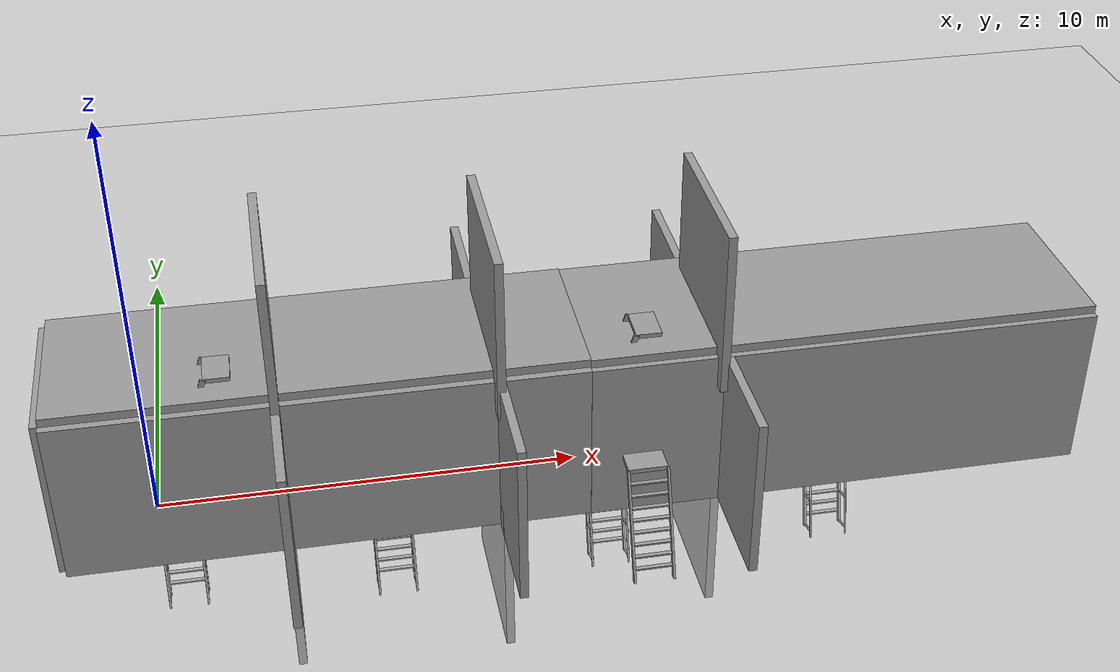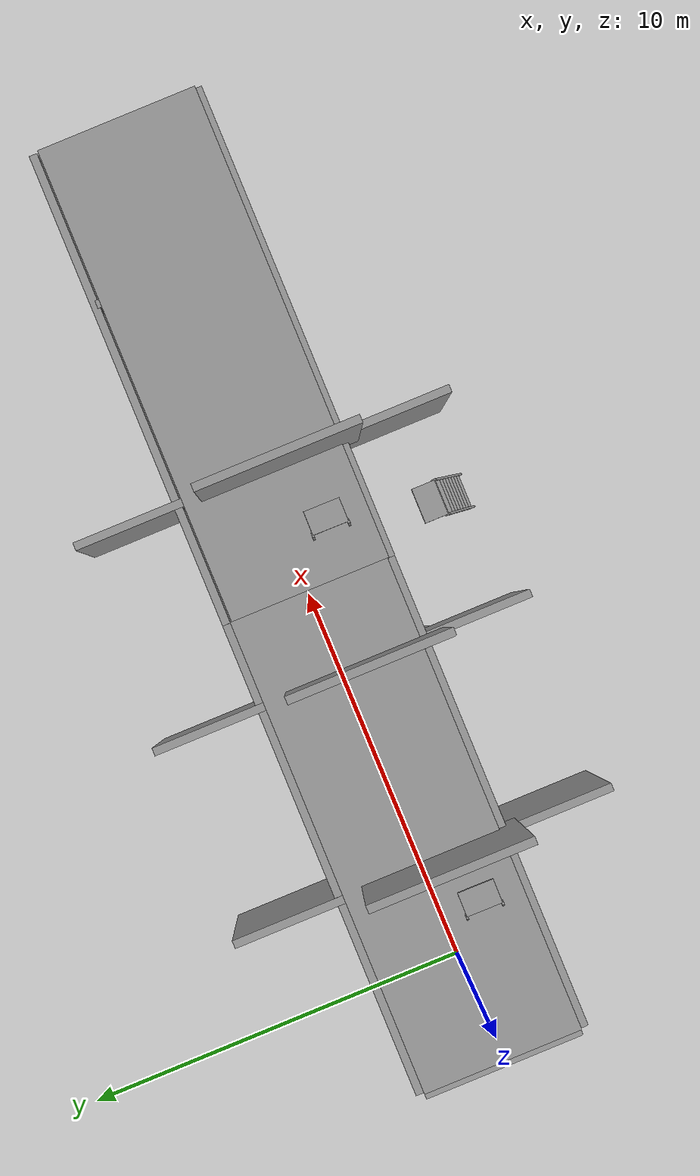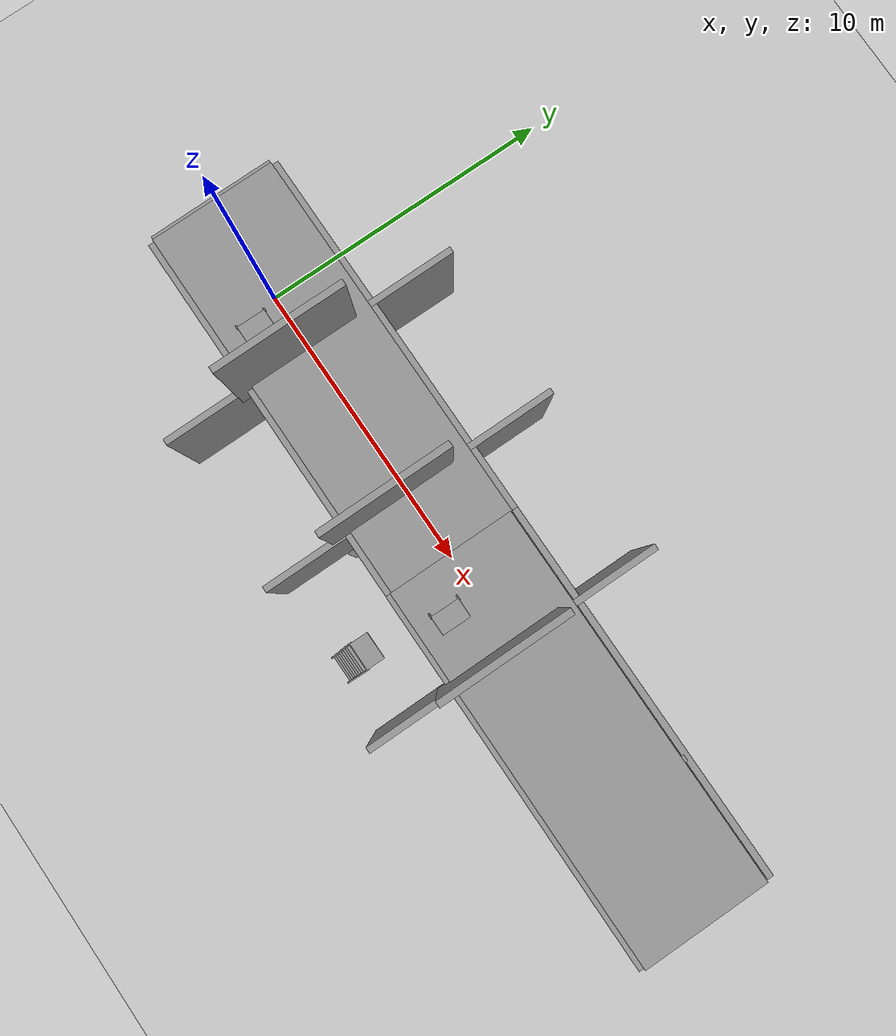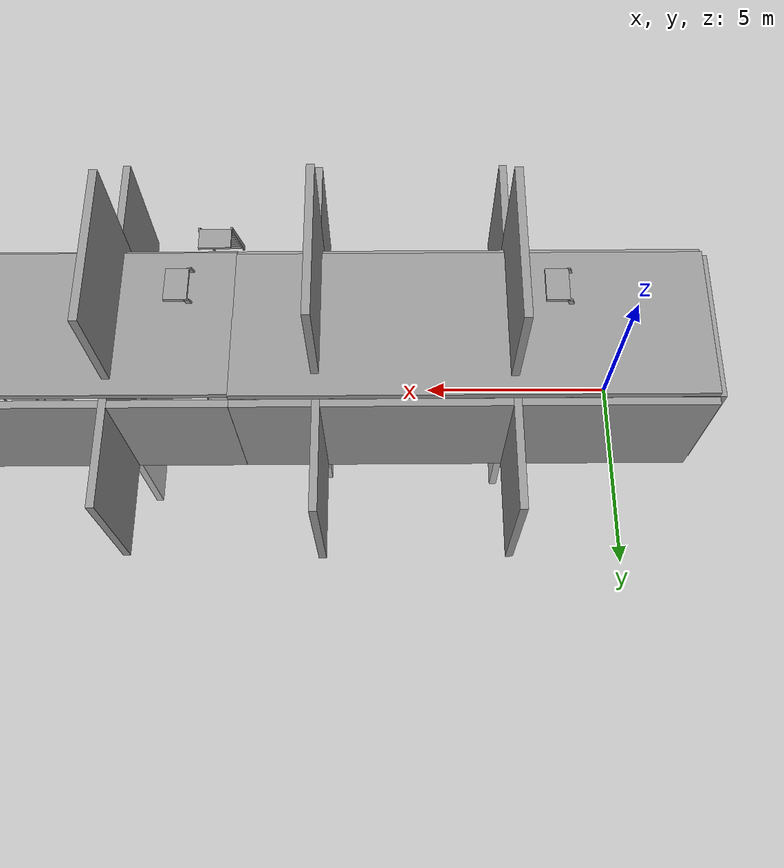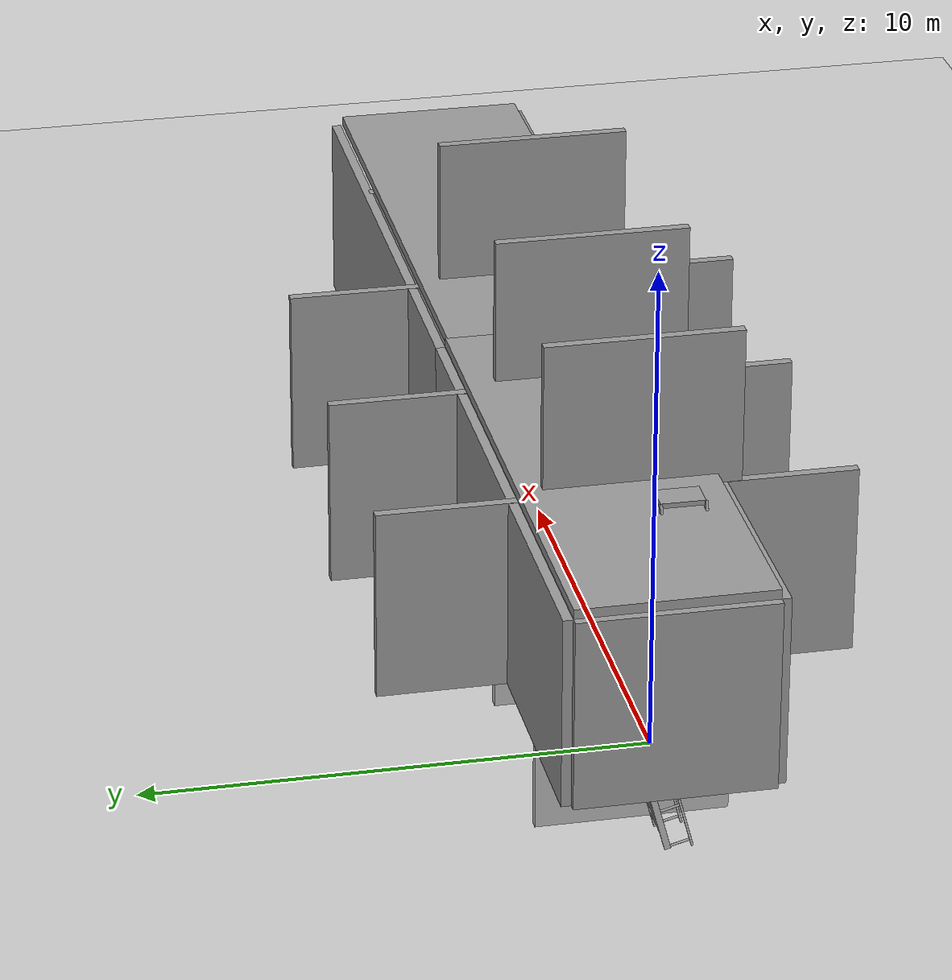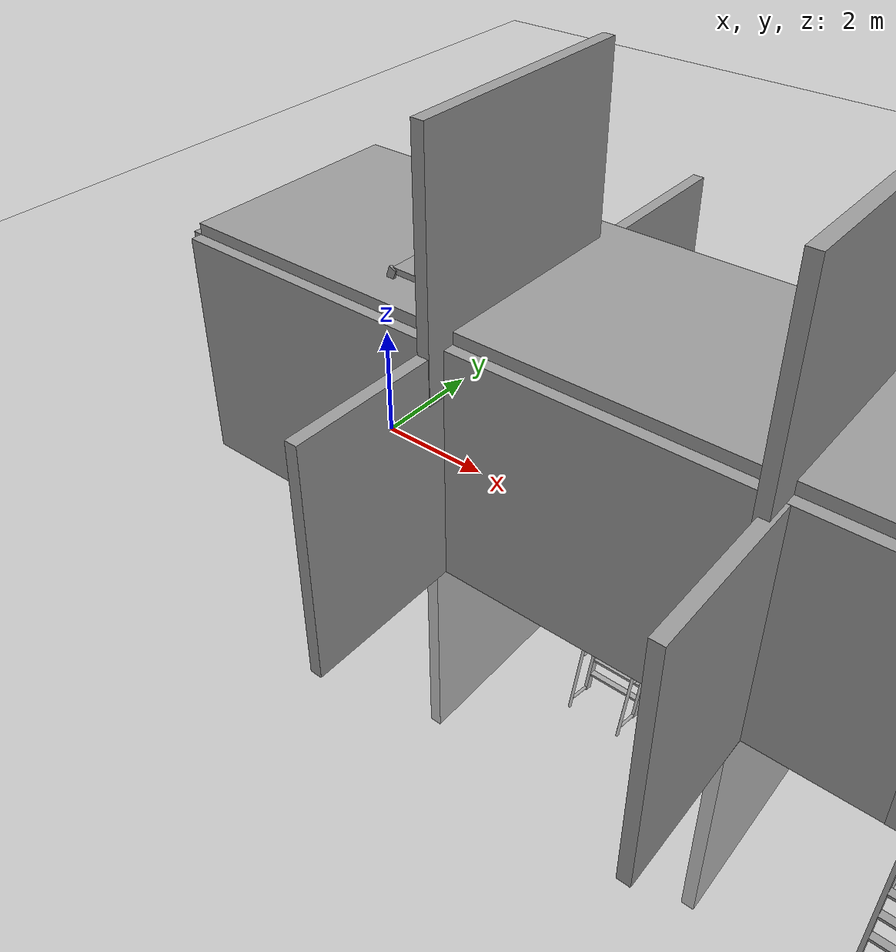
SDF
<sdf version="1.7">
 <world name="default">
  <light name="sun" type="directional">
   <pose>0 0 10 0 -0 0</pose>
   <diffuse>0.8 0.8 0.8 1</diffuse>
   <specular>0.2 0.2 0.2 1</specular>
   <attenuation>
    <range>1000</range>
    <constant>0.9</constant>
    <linear>0.01</linear>
    <quadratic>0.001</quadratic>
   </attenuation>
   <direction>-0.5 0.1 -0.9</direction>
   <spot><inner_angle>0</inner_angle><outer_angle>0</outer_angle><falloff>0</falloff></spot>
  </light>
  <plugin name="ros_interface_plugin" filename="librotors_gazebo_ros_interface_plugin.so"/>
  <model name="ground_plane">
   <static>1</static>
   <link name="link">
    <collision name="collision">
     <geometry><plane><normal>0 0 1</normal><size>100 100</size></plane></geometry>
     <surface>
      <contact><collide_bitmask>65535</collide_bitmask></contact>
      <friction><ode><mu>100</mu><mu2>50</mu2></ode></friction>
     </surface>
    </collision>
    <visual name="visual">
     <cast_shadows>0</cast_shadows>
     <geometry><plane><normal>0 0 1</normal><size>100 100</size></plane></geometry>
     <material>
      <script><uri>file://media/materials/scripts/gazebo.material</uri><name>Gazebo/Grey</name></script>
     </material>
    </visual>
   </link>
  </model>
  <gravity>0 0 -9.8</gravity>
  <magnetic_field>6e-06 2.3e-05 -4.2e-05</magnetic_field>
  <atmosphere type="adiabatic"/>
  <physics type="ode">
   <max_step_size>0.001</max_step_size>
   <real_time_factor>1</real_time_factor>
   <real_time_update_rate>1000</real_time_update_rate>
  </physics>
  <scene><ambient>0.4 0.4 0.4 1</ambient><background>0.7 0.7 0.7 1</background><shadows>1</shadows></scene>
  <spherical_coordinates>
   <surface_model>EARTH_WGS84</surface_model>
   <latitude_deg>0</latitude_deg>
   <longitude_deg>0</longitude_deg>
   <elevation>0</elevation>
   <heading_deg>0</heading_deg>
  </spherical_coordinates>
  <model name="grey_wall">
   <static>1</static>
   <link name="link">
    <pose>0 0 2 0 -0 0</pose>
    <collision name="collision"><geometry><box><size>12 0.2 4</size></box></geometry></collision>
    <visual name="visual">
     <cast_shadows>0</cast_shadows>
     <geometry><box><size>12 0.2 4</size></box></geometry>
     <material><script><name>vrc/grey_wall</name><uri>__default__</uri></script></material>
    </visual>
   </link>
   <pose>4.00391 -2.09108 0.00243 0 -0 0</pose>
  </model>
  <model name="grey_wall_clone">
   <static>1</static>
   <link name="link">
    <pose>0 0 2 0 -0 0</pose>
    <collision name="collision"><geometry><box><size>12 0.2 4</size></box></geometry></collision>
    <visual name="visual">
     <cast_shadows>0</cast_shadows>
     <geometry><box><size>12 0.2 4</size></box></geometry>
     <material><script><name>vrc/grey_wall</name><uri>__default__</uri></script></material>
    </visual>
   </link>
   <pose>4.00436 2.10473 -0.00644 0 -0 0</pose>
  </model>
  <model name="grey_wall_0">
   <static>1</static>
   <link name="link">
    <pose>0 0 2 0 -0 0</pose>
    <collision name="collision"><geometry><box><size>0.2 4 4</size></box></geometry></collision>
    <visual name="visual">
     <cast_shadows>0</cast_shadows>
     <geometry><box><size>0.2 4 4</size></box></geometry>
     <material><script><name>vrc/grey_wall</name><uri>__default__</uri></script></material>
    </visual>
   </link>
   <pose>-2.06266 0.005122 0 0 -0 0</pose>
  </model>
  <model name="grey_wall_0_clone">
   <static>1</static>
   <link name="link">
    <pose>0 0 2 0 -0 0</pose>
    <collision name="collision"><geometry><box><size>0.2 4 4</size></box></geometry></collision>
    <visual name="visual">
     <cast_shadows>0</cast_shadows>
     <geometry><box><size>0.2 4 4</size></box></geometry>
     <material><script><name>vrc/grey_wall</name><uri>__default__</uri></script></material>
    </visual>
   </link>
   <pose>18.1609 0.067045 0 0 -0 0</pose>
  </model>
  <model name="grey_wall_0_clone_0">
   <static>1</static>
   <link name="link">
    <pose>0 0 2 0 -0 0</pose>
    <collision name="collision"><geometry><box><size>0.2 4 4</size></box></geometry></collision>
    <visual name="visual">
     <cast_shadows>0</cast_shadows>
     <geometry><box><size>0.2 4 4</size></box></geometry>
     <material><script><name>vrc/grey_wall</name><uri>__default__</uri></script></material>
    </visual>
   </link>
   <pose>2.94625 2.82856 0 0 -0 0</pose>
  </model>
  <model name="grey_wall_0_clone_1">
   <static>1</static>
   <link name="link">
    <pose>0 0 2 0 -0 0</pose>
    <collision name="collision"><geometry><box><size>0.2 4 4</size></box></geometry></collision>
    <visual name="visual">
     <cast_shadows>0</cast_shadows>
     <geometry><box><size>0.2 4 4</size></box></geometry>
     <material><script><name>vrc/grey_wall</name><uri>__default__</uri></script></material>
    </visual>
   </link>
   <pose>7.87479 2.84716 0 0 -0 0</pose>
  </model>
  <model name="grey_wall_0_clone_2">
   <static>1</static>
   <link name="link">
    <pose>0 0 2 0 -0 0</pose>
    <collision name="collision"><geometry><box><size>0.2 4 4</size></box></geometry></collision>
    <visual name="visual">
     <cast_shadows>0</cast_shadows>
     <geometry><box><size>0.2 4 4</size></box></geometry>
     <material><script><name>vrc/grey_wall</name><uri>__default__</uri></script></material>
    </visual>
   </link>
   <pose>2.98969 -2.86611 0 0 -0 0</pose>
  </model>
  <model name="grey_wall_0_clone_3">
   <static>1</static>
   <link name="link">
    <pose>0 0 2 0 -0 0</pose>
    <collision name="collision"><geometry><box><size>0.2 4 4</size></box></geometry></collision>
    <visual name="visual">
     <cast_shadows>0</cast_shadows>
     <geometry><box><size>0.2 4 4</size></box></geometry>
     <material><script><name>vrc/grey_wall</name><uri>__default__</uri></script></material>
    </visual>
   </link>
   <pose>7.95689 -2.83465 0 0 -0 0</pose>
  </model>
  <model name="grey_wall_1">
   <static>1</static>
   <link name="link">
    <pose>0 0 2 0 -0 0</pose>
    <collision name="collision"><geometry><box><size>12 4 0.2</size></box></geometry></collision>
    <visual name="visual">
     <cast_shadows>0</cast_shadows>
     <geometry><box><size>12 4 0.2</size></box></geometry>
     <material><script><name>vrc/grey_wall</name><uri>__default__</uri></script></material>
    </visual>
   </link>
   <pose>4.01388 -0.000588 2.09857 0 -0 0</pose>
  </model>
  <model name="grey_wall_clone_clone">
   <static>1</static>
   <link name="link">
    <pose>0 0 2 0 -0 0</pose>
    <collision name="collision"><geometry><box><size>12 0.2 4</size></box></geometry></collision>
    <visual name="visual">
     <cast_shadows>0</cast_shadows>
     <geometry><box><size>12 0.2 4</size></box></geometry>
     <material><script><name>vrc/grey_wall</name><uri>__default__</uri></script></material>
    </visual>
   </link>
   <pose>16.0069 2.10317 -0.00644 0 -0 0</pose>
  </model>
  <model name="grey_wall_clone_0">
   <static>1</static>
   <link name="link">
    <pose>0 0 2 0 -0 0</pose>
    <collision name="collision"><geometry><box><size>12 0.2 4</size></box></geometry></collision>
    <visual name="visual">
     <cast_shadows>0</cast_shadows>
     <geometry><box><size>12 0.2 4</size></box></geometry>
     <material><script><name>vrc/grey_wall</name><uri>__default__</uri></script></material>
    </visual>
   </link>
   <pose>15.9969 -2.09749 0.00243 0 -0 0</pose>
  </model>
  <model name="grey_wall_0_clone_1_clone">
   <static>1</static>
   <link name="link">
    <pose>0 0 2 0 -0 0</pose>
    <collision name="collision"><geometry><box><size>0.2 4 4</size></box></geometry></collision>
    <visual name="visual">
     <cast_shadows>0</cast_shadows>
     <geometry><box><size>0.2 4 4</size></box></geometry>
     <material><script><name>vrc/grey_wall</name><uri>__default__</uri></script></material>
    </visual>
   </link>
   <pose>13.0714 2.72769 0 0 -0 0</pose>
  </model>
  <model name="grey_wall_0_clone_1_clone_0">
   <static>1</static>
   <link name="link">
    <pose>0 0 2 0 -0 0</pose>
    <collision name="collision"><geometry><box><size>0.2 4 4</size></box></geometry></collision>
    <visual name="visual">
     <cast_shadows>0</cast_shadows>
     <geometry><box><size>0.2 4 4</size></box></geometry>
     <material><script><name>vrc/grey_wall</name><uri>__default__</uri></script></material>
    </visual>
   </link>
   <pose>13.156 -2.91545 0 0 -0 0</pose>
  </model>
  <model name="grey_wall_0_clone_1_clone_0_clone">
   <static>1</static>
   <link name="link">
    <pose>0 0 2 0 -0 0</pose>
    <collision name="collision"><geometry><box><size>0.2 4 4</size></box></geometry></collision>
    <visual name="visual">
     <cast_shadows>0</cast_shadows>
     <geometry><box><size>0.2 4 4</size></box></geometry>
     <material><script><name>vrc/grey_wall</name><uri>__default__</uri></script></material>
    </visual>
   </link>
   <pose>12.9912 -0.468476 3.25039 0 -0 0</pose>
  </model>
  <model name="grey_wall_0_clone_1_clone_0_clone_clone">
   <static>1</static>
   <link name="link">
    <pose>0 0 2 0 -0 0</pose>
    <collision name="collision"><geometry><box><size>0.2 4 4</size></box></geometry></collision>
    <visual name="visual">
     <cast_shadows>0</cast_shadows>
     <geometry><box><size>0.2 4 4</size></box></geometry>
     <material><script><name>vrc/grey_wall</name><uri>__default__</uri></script></material>
    </visual>
   </link>
   <pose>7.90163 -0.590147 3.25039 0 -0 0</pose>
  </model>
  <model name="grey_wall_0_clone_1_clone_0_clone_clone_0">
   <static>1</static>
   <link name="link">
    <pose>0 0 2 0 -0 0</pose>
    <collision name="collision"><geometry><box><size>0.2 4 4</size></box></geometry></collision>
    <visual name="visual">
     <cast_shadows>0</cast_shadows>
     <geometry><box><size>0.2 4 4</size></box></geometry>
     <material><script><name>vrc/grey_wall</name><uri>__default__</uri></script></material>
    </visual>
   </link>
   <pose>2.99979 -0.490015 3.25039 0 -0 0</pose>
  </model>
  <model name="grey_wall_0_clone_1_clone_0_clone_clone_1">
   <static>1</static>
   <link name="link">
    <pose>0 0 2 0 -0 0</pose>
    <collision name="collision"><geometry><box><size>0.2 4 4</size></box></geometry></collision>
    <visual name="visual">
     <cast_shadows>0</cast_shadows>
     <geometry><box><size>0.2 4 4</size></box></geometry>
     <material><script><name>vrc/grey_wall</name><uri>__default__</uri></script></material>
    </visual>
   </link>
   <pose>13.0698 0.073294 -3.38849 0 -0 0</pose>
  </model>
  <model name="grey_wall_0_clone_1_clone_0_clone_clone_1_clone">
   <static>1</static>
   <link name="link">
    <pose>0 0 2 0 -0 0</pose>
    <collision name="collision"><geometry><box><size>0.2 4 4</size></box></geometry></collision>
    <visual name="visual">
     <cast_shadows>0</cast_shadows>
     <geometry><box><size>0.2 4 4</size></box></geometry>
     <material><script><name>vrc/grey_wall</name><uri>__default__</uri></script></material>
    </visual>
   </link>
   <pose>7.95608 -0.613712 -3.38849 0 -0 0</pose>
  </model>
  <model name="grey_wall_0_clone_1_clone_0_clone_clone_1_clone_0">
   <static>1</static>
   <link name="link">
    <pose>0 0 2 0 -0 0</pose>
    <collision name="collision"><geometry><box><size>0.2 4 4</size></box></geometry></collision>
    <visual name="visual">
     <cast_shadows>0</cast_shadows>
     <geometry><box><size>0.2 4 4</size></box></geometry>
     <material><script><name>vrc/grey_wall</name><uri>__default__</uri></script></material>
    </visual>
   </link>
   <pose>2.97984 -0.384429 -3.38849 0 -0 0</pose>
  </model>
  <model name="grey_wall_1_clone">
   <static>1</static>
   <link name="link">
    <pose>0 0 2 0 -0 0</pose>
    <collision name="collision"><geometry><box><size>12 4 0.2</size></box></geometry></collision>
    <visual name="visual">
     <cast_shadows>0</cast_shadows>
     <geometry><box><size>12 4 0.2</size></box></geometry>
     <material><script><name>vrc/grey_wall</name><uri>__default__</uri></script></material>
    </visual>
   </link>
   <pose>15.9987 -0.040014 2.09857 0 -0 0</pose>
  </model>
  <model name="ladder_70deg_0rails">
   <static>1</static>
   <link name="step0">
    <pose>0 0.097059 0.266667 0 -0 0</pose>
    <inertial>
     <mass>9.75482</mass>
     <inertia>
      <ixx>0.00957124</ixx>
      <iyy>0.65963</iyy>
      <izz>0.666842</izz>
      <ixy>0</ixy>
      <ixz>0</ixz>
      <iyz>0</iyz>
     </inertia>
    </inertial>
    <collision name="collision"><geometry><box><size>0.9 0.1016 0.0381</size></box></geometry></collision>
    <visual name="visual">
     <geometry><box><size>0.9 0.1016 0.0381</size></box></geometry>
     <material>
      <script><uri>file://media/materials/scripts/gazebo.material</uri><name>Gazebo/Grey</name></script>
     </material>
    </visual>
   </link>
   <link name="step1">
    <pose>0 0.194117 0.533333 0 -0 0</pose>
    <inertial>
     <mass>9.75482</mass>
     <inertia>
      <ixx>0.00957124</ixx>
      <iyy>0.65963</iyy>
      <izz>0.666842</izz>
      <ixy>0</ixy>
      <ixz>0</ixz>
      <iyz>0</iyz>
     </inertia>
    </inertial>
    <collision name="collision"><geometry><box><size>0.9 0.1016 0.0381</size></box></geometry></collision>
    <visual name="visual">
     <geometry><box><size>0.9 0.1016 0.0381</size></box></geometry>
     <material>
      <script><uri>file://media/materials/scripts/gazebo.material</uri><name>Gazebo/Grey</name></script>
     </material>
    </visual>
   </link>
   <link name="step2">
    <pose>0 0.291176 0.8 0 -0 0</pose>
    <inertial>
     <mass>9.75482</mass>
     <inertia>
      <ixx>0.00957124</ixx>
      <iyy>0.65963</iyy>
      <izz>0.666842</izz>
      <ixy>0</ixy>
      <ixz>0</ixz>
      <iyz>0</iyz>
     </inertia>
    </inertial>
    <collision name="collision"><geometry><box><size>0.9 0.1016 0.0381</size></box></geometry></collision>
    <visual name="visual">
     <geometry><box><size>0.9 0.1016 0.0381</size></box></geometry>
     <material>
      <script><uri>file://media/materials/scripts/gazebo.material</uri><name>Gazebo/Grey</name></script>
     </material>
    </visual>
   </link>
   <link name="step3">
    <pose>0 0.388235 1.06667 0 -0 0</pose>
    <inertial>
     <mass>9.75482</mass>
     <inertia>
      <ixx>0.00957124</ixx>
      <iyy>0.65963</iyy>
      <izz>0.666842</izz>
      <ixy>0</ixy>
      <ixz>0</ixz>
      <iyz>0</iyz>
     </inertia>
    </inertial>
    <collision name="collision"><geometry><box><size>0.9 0.1016 0.0381</size></box></geometry></collision>
    <visual name="visual">
     <geometry><box><size>0.9 0.1016 0.0381</size></box></geometry>
     <material>
      <script><uri>file://media/materials/scripts/gazebo.material</uri><name>Gazebo/Grey</name></script>
     </material>
    </visual>
   </link>
   <link name="step4">
    <pose>0 0.485294 1.33333 0 -0 0</pose>
    <inertial>
     <mass>9.75482</mass>
     <inertia>
      <ixx>0.00957124</ixx>
      <iyy>0.65963</iyy>
      <izz>0.666842</izz>
      <ixy>0</ixy>
      <ixz>0</ixz>
      <iyz>0</iyz>
     </inertia>
    </inertial>
    <collision name="collision"><geometry><box><size>0.9 0.1016 0.0381</size></box></geometry></collision>
    <visual name="visual">
     <geometry><box><size>0.9 0.1016 0.0381</size></box></geometry>
     <material>
      <script><uri>file://media/materials/scripts/gazebo.material</uri><name>Gazebo/Grey</name></script>
     </material>
    </visual>
   </link>
   <link name="step5">
    <pose>0 0.582352 1.6 0 -0 0</pose>
    <inertial>
     <mass>9.75482</mass>
     <inertia>
      <ixx>0.00957124</ixx>
      <iyy>0.65963</iyy>
      <izz>0.666842</izz>
      <ixy>0</ixy>
      <ixz>0</ixz>
      <iyz>0</iyz>
     </inertia>
    </inertial>
    <collision name="collision"><geometry><box><size>0.9 0.1016 0.0381</size></box></geometry></collision>
    <visual name="visual">
     <geometry><box><size>0.9 0.1016 0.0381</size></box></geometry>
     <material>
      <script><uri>file://media/materials/scripts/gazebo.material</uri><name>Gazebo/Grey</name></script>
     </material>
    </visual>
   </link>
   <link name="step6">
    <pose>0 0.679411 1.86667 0 -0 0</pose>
    <inertial>
     <mass>9.75482</mass>
     <inertia>
      <ixx>0.00957124</ixx>
      <iyy>0.65963</iyy>
      <izz>0.666842</izz>
      <ixy>0</ixy>
      <ixz>0</ixz>
      <iyz>0</iyz>
     </inertia>
    </inertial>
    <collision name="collision"><geometry><box><size>0.9 0.1016 0.0381</size></box></geometry></collision>
    <visual name="visual">
     <geometry><box><size>0.9 0.1016 0.0381</size></box></geometry>
     <material>
      <script><uri>file://media/materials/scripts/gazebo.material</uri><name>Gazebo/Grey</name></script>
     </material>
    </visual>
   </link>
   <link name="step7">
    <pose>0 0.77647 2.13333 0 -0 0</pose>
    <inertial>
     <mass>9.75482</mass>
     <inertia>
      <ixx>0.00957124</ixx>
      <iyy>0.65963</iyy>
      <izz>0.666842</izz>
      <ixy>0</ixy>
      <ixz>0</ixz>
      <iyz>0</iyz>
     </inertia>
    </inertial>
    <collision name="collision"><geometry><box><size>0.9 0.1016 0.0381</size></box></geometry></collision>
    <visual name="visual">
     <geometry><box><size>0.9 0.1016 0.0381</size></box></geometry>
     <material>
      <script><uri>file://media/materials/scripts/gazebo.material</uri><name>Gazebo/Grey</name></script>
     </material>
    </visual>
   </link>
   <link name="landing">
    <pose>0 1.17353 2.4 0 -0 0</pose>
    <inertial>
     <mass>57.6072</mass>
     <inertia><ixx>1.73518</ixx><iyy>3.89545</iyy><izz>5.6167</izz><ixy>0</ixy><ixz>0</ixz><iyz>0</iyz></inertia>
    </inertial>
    <collision name="collision"><geometry><box><size>0.9 0.6 0.1016</size></box></geometry></collision>
    <visual name="visual">
     <geometry><box><size>0.9 0.6 0.1016</size></box></geometry>
     <material>
      <script><uri>file://media/materials/scripts/gazebo.material</uri><name>Gazebo/Grey</name></script>
     </material>
    </visual>
   </link>
   <link name="left_side_wall">
    <pose>-0.45 0.436764 1.2 1.22173 -0 0</pose>
    <collision name="collision"><geometry><box><size>0.0508 2.63403 0.13</size></box></geometry></collision>
    <visual name="visual">
     <geometry><box><size>0.0508 2.63403 0.13</size></box></geometry>
     <material>
      <script><uri>file://media/materials/scripts/gazebo.material</uri><name>Gazebo/Grey</name></script>
     </material>
    </visual>
   </link>
   <link name="right_side_wall">
    <pose>0.45 0.436764 1.2 1.22173 -0 0</pose>
    <collision name="collision"><geometry><box><size>0.0508 2.63403 0.13</size></box></geometry></collision>
    <visual name="visual">
     <geometry><box><size>0.0508 2.63403 0.13</size></box></geometry>
     <material>
      <script><uri>file://media/materials/scripts/gazebo.material</uri><name>Gazebo/Grey</name></script>
     </material>
    </visual>
   </link>
   <pose>0.644209 -0.952347 1.92455 0 0 -1.5783</pose>
  </model>
  <model name="ladder_70deg_0rails_clone">
   <static>1</static>
   <link name="step0">
    <pose>0 0.097059 0.266667 0 -0 0</pose>
    <inertial>
     <mass>9.75482</mass>
     <inertia>
      <ixx>0.00957124</ixx>
      <iyy>0.65963</iyy>
      <izz>0.666842</izz>
      <ixy>0</ixy>
      <ixz>0</ixz>
      <iyz>0</iyz>
     </inertia>
    </inertial>
    <collision name="collision"><geometry><box><size>0.9 0.1016 0.0381</size></box></geometry></collision>
    <visual name="visual">
     <geometry><box><size>0.9 0.1016 0.0381</size></box></geometry>
     <material>
      <script><uri>file://media/materials/scripts/gazebo.material</uri><name>Gazebo/Grey</name></script>
     </material>
    </visual>
   </link>
   <link name="step1">
    <pose>0 0.194117 0.533333 0 -0 0</pose>
    <inertial>
     <mass>9.75482</mass>
     <inertia>
      <ixx>0.00957124</ixx>
      <iyy>0.65963</iyy>
      <izz>0.666842</izz>
      <ixy>0</ixy>
      <ixz>0</ixz>
      <iyz>0</iyz>
     </inertia>
    </inertial>
    <collision name="collision"><geometry><box><size>0.9 0.1016 0.0381</size></box></geometry></collision>
    <visual name="visual">
     <geometry><box><size>0.9 0.1016 0.0381</size></box></geometry>
     <material>
      <script><uri>file://media/materials/scripts/gazebo.material</uri><name>Gazebo/Grey</name></script>
     </material>
    </visual>
   </link>
   <link name="step2">
    <pose>0 0.291176 0.8 0 -0 0</pose>
    <inertial>
     <mass>9.75482</mass>
     <inertia>
      <ixx>0.00957124</ixx>
      <iyy>0.65963</iyy>
      <izz>0.666842</izz>
      <ixy>0</ixy>
      <ixz>0</ixz>
      <iyz>0</iyz>
     </inertia>
    </inertial>
    <collision name="collision"><geometry><box><size>0.9 0.1016 0.0381</size></box></geometry></collision>
    <visual name="visual">
     <geometry><box><size>0.9 0.1016 0.0381</size></box></geometry>
     <material>
      <script><uri>file://media/materials/scripts/gazebo.material</uri><name>Gazebo/Grey</name></script>
     </material>
    </visual>
   </link>
   <link name="step3">
    <pose>0 0.388235 1.06667 0 -0 0</pose>
    <inertial>
     <mass>9.75482</mass>
     <inertia>
      <ixx>0.00957124</ixx>
      <iyy>0.65963</iyy>
      <izz>0.666842</izz>
      <ixy>0</ixy>
      <ixz>0</ixz>
      <iyz>0</iyz>
     </inertia>
    </inertial>
    <collision name="collision"><geometry><box><size>0.9 0.1016 0.0381</size></box></geometry></collision>
    <visual name="visual">
     <geometry><box><size>0.9 0.1016 0.0381</size></box></geometry>
     <material>
      <script><uri>file://media/materials/scripts/gazebo.material</uri><name>Gazebo/Grey</name></script>
     </material>
    </visual>
   </link>
   <link name="step4">
    <pose>0 0.485294 1.33333 0 -0 0</pose>
    <inertial>
     <mass>9.75482</mass>
     <inertia>
      <ixx>0.00957124</ixx>
      <iyy>0.65963</iyy>
      <izz>0.666842</izz>
      <ixy>0</ixy>
      <ixz>0</ixz>
      <iyz>0</iyz>
     </inertia>
    </inertial>
    <collision name="collision"><geometry><box><size>0.9 0.1016 0.0381</size></box></geometry></collision>
    <visual name="visual">
     <geometry><box><size>0.9 0.1016 0.0381</size></box></geometry>
     <material>
      <script><uri>file://media/materials/scripts/gazebo.material</uri><name>Gazebo/Grey</name></script>
     </material>
    </visual>
   </link>
   <link name="step5">
    <pose>0 0.582352 1.6 0 -0 0</pose>
    <inertial>
     <mass>9.75482</mass>
     <inertia>
      <ixx>0.00957124</ixx>
      <iyy>0.65963</iyy>
      <izz>0.666842</izz>
      <ixy>0</ixy>
      <ixz>0</ixz>
      <iyz>0</iyz>
     </inertia>
    </inertial>
    <collision name="collision"><geometry><box><size>0.9 0.1016 0.0381</size></box></geometry></collision>
    <visual name="visual">
     <geometry><box><size>0.9 0.1016 0.0381</size></box></geometry>
     <material>
      <script><uri>file://media/materials/scripts/gazebo.material</uri><name>Gazebo/Grey</name></script>
     </material>
    </visual>
   </link>
   <link name="step6">
    <pose>0 0.679411 1.86667 0 -0 0</pose>
    <inertial>
     <mass>9.75482</mass>
     <inertia>
      <ixx>0.00957124</ixx>
      <iyy>0.65963</iyy>
      <izz>0.666842</izz>
      <ixy>0</ixy>
      <ixz>0</ixz>
      <iyz>0</iyz>
     </inertia>
    </inertial>
    <collision name="collision"><geometry><box><size>0.9 0.1016 0.0381</size></box></geometry></collision>
    <visual name="visual">
     <geometry><box><size>0.9 0.1016 0.0381</size></box></geometry>
     <material>
      <script><uri>file://media/materials/scripts/gazebo.material</uri><name>Gazebo/Grey</name></script>
     </material>
    </visual>
   </link>
   <link name="step7">
    <pose>0 0.77647 2.13333 0 -0 0</pose>
    <inertial>
     <mass>9.75482</mass>
     <inertia>
      <ixx>0.00957124</ixx>
      <iyy>0.65963</iyy>
      <izz>0.666842</izz>
      <ixy>0</ixy>
      <ixz>0</ixz>
      <iyz>0</iyz>
     </inertia>
    </inertial>
    <collision name="collision"><geometry><box><size>0.9 0.1016 0.0381</size></box></geometry></collision>
    <visual name="visual">
     <geometry><box><size>0.9 0.1016 0.0381</size></box></geometry>
     <material>
      <script><uri>file://media/materials/scripts/gazebo.material</uri><name>Gazebo/Grey</name></script>
     </material>
    </visual>
   </link>
   <link name="landing">
    <pose>0 1.17353 2.4 0 -0 0</pose>
    <inertial>
     <mass>57.6072</mass>
     <inertia><ixx>1.73518</ixx><iyy>3.89545</iyy><izz>5.6167</izz><ixy>0</ixy><ixz>0</ixz><iyz>0</iyz></inertia>
    </inertial>
    <collision name="collision"><geometry><box><size>0.9 0.6 0.1016</size></box></geometry></collision>
    <visual name="visual">
     <geometry><box><size>0.9 0.6 0.1016</size></box></geometry>
     <material>
      <script><uri>file://media/materials/scripts/gazebo.material</uri><name>Gazebo/Grey</name></script>
     </material>
    </visual>
   </link>
   <link name="left_side_wall">
    <pose>-0.45 0.436764 1.2 1.22173 -0 0</pose>
    <collision name="collision"><geometry><box><size>0.0508 2.63403 0.13</size></box></geometry></collision>
    <visual name="visual">
     <geometry><box><size>0.0508 2.63403 0.13</size></box></geometry>
     <material>
      <script><uri>file://media/materials/scripts/gazebo.material</uri><name>Gazebo/Grey</name></script>
     </material>
    </visual>
   </link>
   <link name="right_side_wall">
    <pose>0.45 0.436764 1.2 1.22173 -0 0</pose>
    <collision name="collision"><geometry><box><size>0.0508 2.63403 0.13</size></box></geometry></collision>
    <visual name="visual">
     <geometry><box><size>0.0508 2.63403 0.13</size></box></geometry>
     <material>
      <script><uri>file://media/materials/scripts/gazebo.material</uri><name>Gazebo/Grey</name></script>
     </material>
    </visual>
   </link>
   <pose>10.9223 -4.75146 0 0 -0 0</pose>
  </model>
  <model name="ladder_70deg_0rails_clone_0">
   <static>1</static>
   <link name="step0">
    <pose>0 0.097059 0.266667 0 -0 0</pose>
    <inertial>
     <mass>9.75482</mass>
     <inertia>
      <ixx>0.00957124</ixx>
      <iyy>0.65963</iyy>
      <izz>0.666842</izz>
      <ixy>0</ixy>
      <ixz>0</ixz>
      <iyz>0</iyz>
     </inertia>
    </inertial>
    <collision name="collision"><geometry><box><size>0.9 0.1016 0.0381</size></box></geometry></collision>
    <visual name="visual">
     <geometry><box><size>0.9 0.1016 0.0381</size></box></geometry>
     <material>
      <script><uri>file://media/materials/scripts/gazebo.material</uri><name>Gazebo/Grey</name></script>
     </material>
    </visual>
   </link>
   <link name="step1">
    <pose>0 0.194117 0.533333 0 -0 0</pose>
    <inertial>
     <mass>9.75482</mass>
     <inertia>
      <ixx>0.00957124</ixx>
      <iyy>0.65963</iyy>
      <izz>0.666842</izz>
      <ixy>0</ixy>
      <ixz>0</ixz>
      <iyz>0</iyz>
     </inertia>
    </inertial>
    <collision name="collision"><geometry><box><size>0.9 0.1016 0.0381</size></box></geometry></collision>
    <visual name="visual">
     <geometry><box><size>0.9 0.1016 0.0381</size></box></geometry>
     <material>
      <script><uri>file://media/materials/scripts/gazebo.material</uri><name>Gazebo/Grey</name></script>
     </material>
    </visual>
   </link>
   <link name="step2">
    <pose>0 0.291176 0.8 0 -0 0</pose>
    <inertial>
     <mass>9.75482</mass>
     <inertia>
      <ixx>0.00957124</ixx>
      <iyy>0.65963</iyy>
      <izz>0.666842</izz>
      <ixy>0</ixy>
      <ixz>0</ixz>
      <iyz>0</iyz>
     </inertia>
    </inertial>
    <collision name="collision"><geometry><box><size>0.9 0.1016 0.0381</size></box></geometry></collision>
    <visual name="visual">
     <geometry><box><size>0.9 0.1016 0.0381</size></box></geometry>
     <material>
      <script><uri>file://media/materials/scripts/gazebo.material</uri><name>Gazebo/Grey</name></script>
     </material>
    </visual>
   </link>
   <link name="step3">
    <pose>0 0.388235 1.06667 0 -0 0</pose>
    <inertial>
     <mass>9.75482</mass>
     <inertia>
      <ixx>0.00957124</ixx>
      <iyy>0.65963</iyy>
      <izz>0.666842</izz>
      <ixy>0</ixy>
      <ixz>0</ixz>
      <iyz>0</iyz>
     </inertia>
    </inertial>
    <collision name="collision"><geometry><box><size>0.9 0.1016 0.0381</size></box></geometry></collision>
    <visual name="visual">
     <geometry><box><size>0.9 0.1016 0.0381</size></box></geometry>
     <material>
      <script><uri>file://media/materials/scripts/gazebo.material</uri><name>Gazebo/Grey</name></script>
     </material>
    </visual>
   </link>
   <link name="step4">
    <pose>0 0.485294 1.33333 0 -0 0</pose>
    <inertial>
     <mass>9.75482</mass>
     <inertia>
      <ixx>0.00957124</ixx>
      <iyy>0.65963</iyy>
      <izz>0.666842</izz>
      <ixy>0</ixy>
      <ixz>0</ixz>
      <iyz>0</iyz>
     </inertia>
    </inertial>
    <collision name="collision"><geometry><box><size>0.9 0.1016 0.0381</size></box></geometry></collision>
    <visual name="visual">
     <geometry><box><size>0.9 0.1016 0.0381</size></box></geometry>
     <material>
      <script><uri>file://media/materials/scripts/gazebo.material</uri><name>Gazebo/Grey</name></script>
     </material>
    </visual>
   </link>
   <link name="step5">
    <pose>0 0.582352 1.6 0 -0 0</pose>
    <inertial>
     <mass>9.75482</mass>
     <inertia>
      <ixx>0.00957124</ixx>
      <iyy>0.65963</iyy>
      <izz>0.666842</izz>
      <ixy>0</ixy>
      <ixz>0</ixz>
      <iyz>0</iyz>
     </inertia>
    </inertial>
    <collision name="collision"><geometry><box><size>0.9 0.1016 0.0381</size></box></geometry></collision>
    <visual name="visual">
     <geometry><box><size>0.9 0.1016 0.0381</size></box></geometry>
     <material>
      <script><uri>file://media/materials/scripts/gazebo.material</uri><name>Gazebo/Grey</name></script>
     </material>
    </visual>
   </link>
   <link name="step6">
    <pose>0 0.679411 1.86667 0 -0 0</pose>
    <inertial>
     <mass>9.75482</mass>
     <inertia>
      <ixx>0.00957124</ixx>
      <iyy>0.65963</iyy>
      <izz>0.666842</izz>
      <ixy>0</ixy>
      <ixz>0</ixz>
      <iyz>0</iyz>
     </inertia>
    </inertial>
    <collision name="collision"><geometry><box><size>0.9 0.1016 0.0381</size></box></geometry></collision>
    <visual name="visual">
     <geometry><box><size>0.9 0.1016 0.0381</size></box></geometry>
     <material>
      <script><uri>file://media/materials/scripts/gazebo.material</uri><name>Gazebo/Grey</name></script>
     </material>
    </visual>
   </link>
   <link name="step7">
    <pose>0 0.77647 2.13333 0 -0 0</pose>
    <inertial>
     <mass>9.75482</mass>
     <inertia>
      <ixx>0.00957124</ixx>
      <iyy>0.65963</iyy>
      <izz>0.666842</izz>
      <ixy>0</ixy>
      <ixz>0</ixz>
      <iyz>0</iyz>
     </inertia>
    </inertial>
    <collision name="collision"><geometry><box><size>0.9 0.1016 0.0381</size></box></geometry></collision>
    <visual name="visual">
     <geometry><box><size>0.9 0.1016 0.0381</size></box></geometry>
     <material>
      <script><uri>file://media/materials/scripts/gazebo.material</uri><name>Gazebo/Grey</name></script>
     </material>
    </visual>
   </link>
   <link name="landing">
    <pose>0 1.17353 2.4 0 -0 0</pose>
    <inertial>
     <mass>57.6072</mass>
     <inertia><ixx>1.73518</ixx><iyy>3.89545</iyy><izz>5.6167</izz><ixy>0</ixy><ixz>0</ixz><iyz>0</iyz></inertia>
    </inertial>
    <collision name="collision"><geometry><box><size>0.9 0.6 0.1016</size></box></geometry></collision>
    <visual name="visual">
     <geometry><box><size>0.9 0.6 0.1016</size></box></geometry>
     <material>
      <script><uri>file://media/materials/scripts/gazebo.material</uri><name>Gazebo/Grey</name></script>
     </material>
    </visual>
   </link>
   <link name="left_side_wall">
    <pose>-0.45 0.436764 1.2 1.22173 -0 0</pose>
    <collision name="collision"><geometry><box><size>0.0508 2.63403 0.13</size></box></geometry></collision>
    <visual name="visual">
     <geometry><box><size>0.0508 2.63403 0.13</size></box></geometry>
     <material>
      <script><uri>file://media/materials/scripts/gazebo.material</uri><name>Gazebo/Grey</name></script>
     </material>
    </visual>
   </link>
   <link name="right_side_wall">
    <pose>0.45 0.436764 1.2 1.22173 -0 0</pose>
    <collision name="collision"><geometry><box><size>0.0508 2.63403 0.13</size></box></geometry></collision>
    <visual name="visual">
     <geometry><box><size>0.0508 2.63403 0.13</size></box></geometry>
     <material>
      <script><uri>file://media/materials/scripts/gazebo.material</uri><name>Gazebo/Grey</name></script>
     </material>
    </visual>
   </link>
   <pose>-0.057863 -0.92893 0 0 0 -1.5783</pose>
  </model>
  <model name="ladder_70deg_0rails_clone_0_clone">
   <static>1</static>
   <link name="step0">
    <pose>0 0.097059 0.266667 0 -0 0</pose>
    <inertial>
     <mass>9.75482</mass>
     <inertia>
      <ixx>0.00957124</ixx>
      <iyy>0.65963</iyy>
      <izz>0.666842</izz>
      <ixy>0</ixy>
      <ixz>0</ixz>
      <iyz>0</iyz>
     </inertia>
    </inertial>
    <collision name="collision"><geometry><box><size>0.9 0.1016 0.0381</size></box></geometry></collision>
    <visual name="visual">
     <geometry><box><size>0.9 0.1016 0.0381</size></box></geometry>
     <material>
      <script><uri>file://media/materials/scripts/gazebo.material</uri><name>Gazebo/Grey</name></script>
     </material>
    </visual>
   </link>
   <link name="step1">
    <pose>0 0.194117 0.533333 0 -0 0</pose>
    <inertial>
     <mass>9.75482</mass>
     <inertia>
      <ixx>0.00957124</ixx>
      <iyy>0.65963</iyy>
      <izz>0.666842</izz>
      <ixy>0</ixy>
      <ixz>0</ixz>
      <iyz>0</iyz>
     </inertia>
    </inertial>
    <collision name="collision"><geometry><box><size>0.9 0.1016 0.0381</size></box></geometry></collision>
    <visual name="visual">
     <geometry><box><size>0.9 0.1016 0.0381</size></box></geometry>
     <material>
      <script><uri>file://media/materials/scripts/gazebo.material</uri><name>Gazebo/Grey</name></script>
     </material>
    </visual>
   </link>
   <link name="step2">
    <pose>0 0.291176 0.8 0 -0 0</pose>
    <inertial>
     <mass>9.75482</mass>
     <inertia>
      <ixx>0.00957124</ixx>
      <iyy>0.65963</iyy>
      <izz>0.666842</izz>
      <ixy>0</ixy>
      <ixz>0</ixz>
      <iyz>0</iyz>
     </inertia>
    </inertial>
    <collision name="collision"><geometry><box><size>0.9 0.1016 0.0381</size></box></geometry></collision>
    <visual name="visual">
     <geometry><box><size>0.9 0.1016 0.0381</size></box></geometry>
     <material>
      <script><uri>file://media/materials/scripts/gazebo.material</uri><name>Gazebo/Grey</name></script>
     </material>
    </visual>
   </link>
   <link name="step3">
    <pose>0 0.388235 1.06667 0 -0 0</pose>
    <inertial>
     <mass>9.75482</mass>
     <inertia>
      <ixx>0.00957124</ixx>
      <iyy>0.65963</iyy>
      <izz>0.666842</izz>
      <ixy>0</ixy>
      <ixz>0</ixz>
      <iyz>0</iyz>
     </inertia>
    </inertial>
    <collision name="collision"><geometry><box><size>0.9 0.1016 0.0381</size></box></geometry></collision>
    <visual name="visual">
     <geometry><box><size>0.9 0.1016 0.0381</size></box></geometry>
     <material>
      <script><uri>file://media/materials/scripts/gazebo.material</uri><name>Gazebo/Grey</name></script>
     </material>
    </visual>
   </link>
   <link name="step4">
    <pose>0 0.485294 1.33333 0 -0 0</pose>
    <inertial>
     <mass>9.75482</mass>
     <inertia>
      <ixx>0.00957124</ixx>
      <iyy>0.65963</iyy>
      <izz>0.666842</izz>
      <ixy>0</ixy>
      <ixz>0</ixz>
      <iyz>0</iyz>
     </inertia>
    </inertial>
    <collision name="collision"><geometry><box><size>0.9 0.1016 0.0381</size></box></geometry></collision>
    <visual name="visual">
     <geometry><box><size>0.9 0.1016 0.0381</size></box></geometry>
     <material>
      <script><uri>file://media/materials/scripts/gazebo.material</uri><name>Gazebo/Grey</name></script>
     </material>
    </visual>
   </link>
   <link name="step5">
    <pose>0 0.582352 1.6 0 -0 0</pose>
    <inertial>
     <mass>9.75482</mass>
     <inertia>
      <ixx>0.00957124</ixx>
      <iyy>0.65963</iyy>
      <izz>0.666842</izz>
      <ixy>0</ixy>
      <ixz>0</ixz>
      <iyz>0</iyz>
     </inertia>
    </inertial>
    <collision name="collision"><geometry><box><size>0.9 0.1016 0.0381</size></box></geometry></collision>
    <visual name="visual">
     <geometry><box><size>0.9 0.1016 0.0381</size></box></geometry>
     <material>
      <script><uri>file://media/materials/scripts/gazebo.material</uri><name>Gazebo/Grey</name></script>
     </material>
    </visual>
   </link>
   <link name="step6">
    <pose>0 0.679411 1.86667 0 -0 0</pose>
    <inertial>
     <mass>9.75482</mass>
     <inertia>
      <ixx>0.00957124</ixx>
      <iyy>0.65963</iyy>
      <izz>0.666842</izz>
      <ixy>0</ixy>
      <ixz>0</ixz>
      <iyz>0</iyz>
     </inertia>
    </inertial>
    <collision name="collision"><geometry><box><size>0.9 0.1016 0.0381</size></box></geometry></collision>
    <visual name="visual">
     <geometry><box><size>0.9 0.1016 0.0381</size></box></geometry>
     <material>
      <script><uri>file://media/materials/scripts/gazebo.material</uri><name>Gazebo/Grey</name></script>
     </material>
    </visual>
   </link>
   <link name="step7">
    <pose>0 0.77647 2.13333 0 -0 0</pose>
    <inertial>
     <mass>9.75482</mass>
     <inertia>
      <ixx>0.00957124</ixx>
      <iyy>0.65963</iyy>
      <izz>0.666842</izz>
      <ixy>0</ixy>
      <ixz>0</ixz>
      <iyz>0</iyz>
     </inertia>
    </inertial>
    <collision name="collision"><geometry><box><size>0.9 0.1016 0.0381</size></box></geometry></collision>
    <visual name="visual">
     <geometry><box><size>0.9 0.1016 0.0381</size></box></geometry>
     <material>
      <script><uri>file://media/materials/scripts/gazebo.material</uri><name>Gazebo/Grey</name></script>
     </material>
    </visual>
   </link>
   <link name="landing">
    <pose>0 1.17353 2.4 0 -0 0</pose>
    <inertial>
     <mass>57.6072</mass>
     <inertia><ixx>1.73518</ixx><iyy>3.89545</iyy><izz>5.6167</izz><ixy>0</ixy><ixz>0</ixz><iyz>0</iyz></inertia>
    </inertial>
    <collision name="collision"><geometry><box><size>0.9 0.6 0.1016</size></box></geometry></collision>
    <visual name="visual">
     <geometry><box><size>0.9 0.6 0.1016</size></box></geometry>
     <material>
      <script><uri>file://media/materials/scripts/gazebo.material</uri><name>Gazebo/Grey</name></script>
     </material>
    </visual>
   </link>
   <link name="left_side_wall">
    <pose>-0.45 0.436764 1.2 1.22173 -0 0</pose>
    <collision name="collision"><geometry><box><size>0.0508 2.63403 0.13</size></box></geometry></collision>
    <visual name="visual">
     <geometry><box><size>0.0508 2.63403 0.13</size></box></geometry>
     <material>
      <script><uri>file://media/materials/scripts/gazebo.material</uri><name>Gazebo/Grey</name></script>
     </material>
    </visual>
   </link>
   <link name="right_side_wall">
    <pose>0.45 0.436764 1.2 1.22173 -0 0</pose>
    <collision name="collision"><geometry><box><size>0.0508 2.63403 0.13</size></box></geometry></collision>
    <visual name="visual">
     <geometry><box><size>0.0508 2.63403 0.13</size></box></geometry>
     <material>
      <script><uri>file://media/materials/scripts/gazebo.material</uri><name>Gazebo/Grey</name></script>
     </material>
    </visual>
   </link>
   <pose>9.61991 -1.0182 0 0 0 -1.5783</pose>
  </model>
  <model name="ladder_70deg_0rails_clone_1">
   <static>1</static>
   <link name="step0">
    <pose>0 0.097059 0.266667 0 -0 0</pose>
    <inertial>
     <mass>9.75482</mass>
     <inertia>
      <ixx>0.00957124</ixx>
      <iyy>0.65963</iyy>
      <izz>0.666842</izz>
      <ixy>0</ixy>
      <ixz>0</ixz>
      <iyz>0</iyz>
     </inertia>
    </inertial>
    <collision name="collision"><geometry><box><size>0.9 0.1016 0.0381</size></box></geometry></collision>
    <visual name="visual">
     <geometry><box><size>0.9 0.1016 0.0381</size></box></geometry>
     <material>
      <script><uri>file://media/materials/scripts/gazebo.material</uri><name>Gazebo/Grey</name></script>
     </material>
    </visual>
   </link>
   <link name="step1">
    <pose>0 0.194117 0.533333 0 -0 0</pose>
    <inertial>
     <mass>9.75482</mass>
     <inertia>
      <ixx>0.00957124</ixx>
      <iyy>0.65963</iyy>
      <izz>0.666842</izz>
      <ixy>0</ixy>
      <ixz>0</ixz>
      <iyz>0</iyz>
     </inertia>
    </inertial>
    <collision name="collision"><geometry><box><size>0.9 0.1016 0.0381</size></box></geometry></collision>
    <visual name="visual">
     <geometry><box><size>0.9 0.1016 0.0381</size></box></geometry>
     <material>
      <script><uri>file://media/materials/scripts/gazebo.material</uri><name>Gazebo/Grey</name></script>
     </material>
    </visual>
   </link>
   <link name="step2">
    <pose>0 0.291176 0.8 0 -0 0</pose>
    <inertial>
     <mass>9.75482</mass>
     <inertia>
      <ixx>0.00957124</ixx>
      <iyy>0.65963</iyy>
      <izz>0.666842</izz>
      <ixy>0</ixy>
      <ixz>0</ixz>
      <iyz>0</iyz>
     </inertia>
    </inertial>
    <collision name="collision"><geometry><box><size>0.9 0.1016 0.0381</size></box></geometry></collision>
    <visual name="visual">
     <geometry><box><size>0.9 0.1016 0.0381</size></box></geometry>
     <material>
      <script><uri>file://media/materials/scripts/gazebo.material</uri><name>Gazebo/Grey</name></script>
     </material>
    </visual>
   </link>
   <link name="step3">
    <pose>0 0.388235 1.06667 0 -0 0</pose>
    <inertial>
     <mass>9.75482</mass>
     <inertia>
      <ixx>0.00957124</ixx>
      <iyy>0.65963</iyy>
      <izz>0.666842</izz>
      <ixy>0</ixy>
      <ixz>0</ixz>
      <iyz>0</iyz>
     </inertia>
    </inertial>
    <collision name="collision"><geometry><box><size>0.9 0.1016 0.0381</size></box></geometry></collision>
    <visual name="visual">
     <geometry><box><size>0.9 0.1016 0.0381</size></box></geometry>
     <material>
      <script><uri>file://media/materials/scripts/gazebo.material</uri><name>Gazebo/Grey</name></script>
     </material>
    </visual>
   </link>
   <link name="step4">
    <pose>0 0.485294 1.33333 0 -0 0</pose>
    <inertial>
     <mass>9.75482</mass>
     <inertia>
      <ixx>0.00957124</ixx>
      <iyy>0.65963</iyy>
      <izz>0.666842</izz>
      <ixy>0</ixy>
      <ixz>0</ixz>
      <iyz>0</iyz>
     </inertia>
    </inertial>
    <collision name="collision"><geometry><box><size>0.9 0.1016 0.0381</size></box></geometry></collision>
    <visual name="visual">
     <geometry><box><size>0.9 0.1016 0.0381</size></box></geometry>
     <material>
      <script><uri>file://media/materials/scripts/gazebo.material</uri><name>Gazebo/Grey</name></script>
     </material>
    </visual>
   </link>
   <link name="step5">
    <pose>0 0.582352 1.6 0 -0 0</pose>
    <inertial>
     <mass>9.75482</mass>
     <inertia>
      <ixx>0.00957124</ixx>
      <iyy>0.65963</iyy>
      <izz>0.666842</izz>
      <ixy>0</ixy>
      <ixz>0</ixz>
      <iyz>0</iyz>
     </inertia>
    </inertial>
    <collision name="collision"><geometry><box><size>0.9 0.1016 0.0381</size></box></geometry></collision>
    <visual name="visual">
     <geometry><box><size>0.9 0.1016 0.0381</size></box></geometry>
     <material>
      <script><uri>file://media/materials/scripts/gazebo.material</uri><name>Gazebo/Grey</name></script>
     </material>
    </visual>
   </link>
   <link name="step6">
    <pose>0 0.679411 1.86667 0 -0 0</pose>
    <inertial>
     <mass>9.75482</mass>
     <inertia>
      <ixx>0.00957124</ixx>
      <iyy>0.65963</iyy>
      <izz>0.666842</izz>
      <ixy>0</ixy>
      <ixz>0</ixz>
      <iyz>0</iyz>
     </inertia>
    </inertial>
    <collision name="collision"><geometry><box><size>0.9 0.1016 0.0381</size></box></geometry></collision>
    <visual name="visual">
     <geometry><box><size>0.9 0.1016 0.0381</size></box></geometry>
     <material>
      <script><uri>file://media/materials/scripts/gazebo.material</uri><name>Gazebo/Grey</name></script>
     </material>
    </visual>
   </link>
   <link name="step7">
    <pose>0 0.77647 2.13333 0 -0 0</pose>
    <inertial>
     <mass>9.75482</mass>
     <inertia>
      <ixx>0.00957124</ixx>
      <iyy>0.65963</iyy>
      <izz>0.666842</izz>
      <ixy>0</ixy>
      <ixz>0</ixz>
      <iyz>0</iyz>
     </inertia>
    </inertial>
    <collision name="collision"><geometry><box><size>0.9 0.1016 0.0381</size></box></geometry></collision>
    <visual name="visual">
     <geometry><box><size>0.9 0.1016 0.0381</size></box></geometry>
     <material>
      <script><uri>file://media/materials/scripts/gazebo.material</uri><name>Gazebo/Grey</name></script>
     </material>
    </visual>
   </link>
   <link name="landing">
    <pose>0 1.17353 2.4 0 -0 0</pose>
    <inertial>
     <mass>57.6072</mass>
     <inertia><ixx>1.73518</ixx><iyy>3.89545</iyy><izz>5.6167</izz><ixy>0</ixy><ixz>0</ixz><iyz>0</iyz></inertia>
    </inertial>
    <collision name="collision"><geometry><box><size>0.9 0.6 0.1016</size></box></geometry></collision>
    <visual name="visual">
     <geometry><box><size>0.9 0.6 0.1016</size></box></geometry>
     <material>
      <script><uri>file://media/materials/scripts/gazebo.material</uri><name>Gazebo/Grey</name></script>
     </material>
    </visual>
   </link>
   <link name="left_side_wall">
    <pose>-0.45 0.436764 1.2 1.22173 -0 0</pose>
    <collision name="collision"><geometry><box><size>0.0508 2.63403 0.13</size></box></geometry></collision>
    <visual name="visual">
     <geometry><box><size>0.0508 2.63403 0.13</size></box></geometry>
     <material>
      <script><uri>file://media/materials/scripts/gazebo.material</uri><name>Gazebo/Grey</name></script>
     </material>
    </visual>
   </link>
   <link name="right_side_wall">
    <pose>0.45 0.436764 1.2 1.22173 -0 0</pose>
    <collision name="collision"><geometry><box><size>0.0508 2.63403 0.13</size></box></geometry></collision>
    <visual name="visual">
     <geometry><box><size>0.0508 2.63403 0.13</size></box></geometry>
     <material>
      <script><uri>file://media/materials/scripts/gazebo.material</uri><name>Gazebo/Grey</name></script>
     </material>
    </visual>
   </link>
   <pose>10.2796 -1.02063 1.92456 0 0 -1.5783</pose>
  </model>
  <model name="ladder_75deg_2rails">
   <static>1</static>
   <link name="step0">
    <pose>0 0.071453 0.266667 0 -0 0</pose>
    <inertial>
     <mass>9.75482</mass>
     <inertia>
      <ixx>0.00957124</ixx>
      <iyy>0.65963</iyy>
      <izz>0.666842</izz>
      <ixy>0</ixy>
      <ixz>0</ixz>
      <iyz>0</iyz>
     </inertia>
    </inertial>
    <collision name="collision"><geometry><box><size>0.9 0.1016 0.0381</size></box></geometry></collision>
    <visual name="visual">
     <geometry><box><size>0.9 0.1016 0.0381</size></box></geometry>
     <material>
      <script><uri>file://media/materials/scripts/gazebo.material</uri><name>Gazebo/Grey</name></script>
     </material>
    </visual>
   </link>
   <link name="step1">
    <pose>0 0.142906 0.533333 0 -0 0</pose>
    <inertial>
     <mass>9.75482</mass>
     <inertia>
      <ixx>0.00957124</ixx>
      <iyy>0.65963</iyy>
      <izz>0.666842</izz>
      <ixy>0</ixy>
      <ixz>0</ixz>
      <iyz>0</iyz>
     </inertia>
    </inertial>
    <collision name="collision"><geometry><box><size>0.9 0.1016 0.0381</size></box></geometry></collision>
    <visual name="visual">
     <geometry><box><size>0.9 0.1016 0.0381</size></box></geometry>
     <material>
      <script><uri>file://media/materials/scripts/gazebo.material</uri><name>Gazebo/Grey</name></script>
     </material>
    </visual>
   </link>
   <link name="step2">
    <pose>0 0.214359 0.8 0 -0 0</pose>
    <inertial>
     <mass>9.75482</mass>
     <inertia>
      <ixx>0.00957124</ixx>
      <iyy>0.65963</iyy>
      <izz>0.666842</izz>
      <ixy>0</ixy>
      <ixz>0</ixz>
      <iyz>0</iyz>
     </inertia>
    </inertial>
    <collision name="collision"><geometry><box><size>0.9 0.1016 0.0381</size></box></geometry></collision>
    <visual name="visual">
     <geometry><box><size>0.9 0.1016 0.0381</size></box></geometry>
     <material>
      <script><uri>file://media/materials/scripts/gazebo.material</uri><name>Gazebo/Grey</name></script>
     </material>
    </visual>
   </link>
   <link name="step3">
    <pose>0 0.285812 1.06667 0 -0 0</pose>
    <inertial>
     <mass>9.75482</mass>
     <inertia>
      <ixx>0.00957124</ixx>
      <iyy>0.65963</iyy>
      <izz>0.666842</izz>
      <ixy>0</ixy>
      <ixz>0</ixz>
      <iyz>0</iyz>
     </inertia>
    </inertial>
    <collision name="collision"><geometry><box><size>0.9 0.1016 0.0381</size></box></geometry></collision>
    <visual name="visual">
     <geometry><box><size>0.9 0.1016 0.0381</size></box></geometry>
     <material>
      <script><uri>file://media/materials/scripts/gazebo.material</uri><name>Gazebo/Grey</name></script>
     </material>
    </visual>
   </link>
   <link name="step4">
    <pose>0 0.357266 1.33333 0 -0 0</pose>
    <inertial>
     <mass>9.75482</mass>
     <inertia>
      <ixx>0.00957124</ixx>
      <iyy>0.65963</iyy>
      <izz>0.666842</izz>
      <ixy>0</ixy>
      <ixz>0</ixz>
      <iyz>0</iyz>
     </inertia>
    </inertial>
    <collision name="collision"><geometry><box><size>0.9 0.1016 0.0381</size></box></geometry></collision>
    <visual name="visual">
     <geometry><box><size>0.9 0.1016 0.0381</size></box></geometry>
     <material>
      <script><uri>file://media/materials/scripts/gazebo.material</uri><name>Gazebo/Grey</name></script>
     </material>
    </visual>
   </link>
   <link name="step5">
    <pose>0 0.428719 1.6 0 -0 0</pose>
    <inertial>
     <mass>9.75482</mass>
     <inertia>
      <ixx>0.00957124</ixx>
      <iyy>0.65963</iyy>
      <izz>0.666842</izz>
      <ixy>0</ixy>
      <ixz>0</ixz>
      <iyz>0</iyz>
     </inertia>
    </inertial>
    <collision name="collision"><geometry><box><size>0.9 0.1016 0.0381</size></box></geometry></collision>
    <visual name="visual">
     <geometry><box><size>0.9 0.1016 0.0381</size></box></geometry>
     <material>
      <script><uri>file://media/materials/scripts/gazebo.material</uri><name>Gazebo/Grey</name></script>
     </material>
    </visual>
   </link>
   <link name="step6">
    <pose>0 0.500172 1.86667 0 -0 0</pose>
    <inertial>
     <mass>9.75482</mass>
     <inertia>
      <ixx>0.00957124</ixx>
      <iyy>0.65963</iyy>
      <izz>0.666842</izz>
      <ixy>0</ixy>
      <ixz>0</ixz>
      <iyz>0</iyz>
     </inertia>
    </inertial>
    <collision name="collision"><geometry><box><size>0.9 0.1016 0.0381</size></box></geometry></collision>
    <visual name="visual">
     <geometry><box><size>0.9 0.1016 0.0381</size></box></geometry>
     <material>
      <script><uri>file://media/materials/scripts/gazebo.material</uri><name>Gazebo/Grey</name></script>
     </material>
    </visual>
   </link>
   <link name="step7">
    <pose>0 0.571625 2.13333 0 -0 0</pose>
    <inertial>
     <mass>9.75482</mass>
     <inertia>
      <ixx>0.00957124</ixx>
      <iyy>0.65963</iyy>
      <izz>0.666842</izz>
      <ixy>0</ixy>
      <ixz>0</ixz>
      <iyz>0</iyz>
     </inertia>
    </inertial>
    <collision name="collision"><geometry><box><size>0.9 0.1016 0.0381</size></box></geometry></collision>
    <visual name="visual">
     <geometry><box><size>0.9 0.1016 0.0381</size></box></geometry>
     <material>
      <script><uri>file://media/materials/scripts/gazebo.material</uri><name>Gazebo/Grey</name></script>
     </material>
    </visual>
   </link>
   <link name="landing">
    <pose>0 0.943078 2.4 0 -0 0</pose>
    <inertial>
     <mass>57.6072</mass>
     <inertia><ixx>1.73518</ixx><iyy>3.89545</iyy><izz>5.6167</izz><ixy>0</ixy><ixz>0</ixz><iyz>0</iyz></inertia>
    </inertial>
    <collision name="collision"><geometry><box><size>0.9 0.6 0.1016</size></box></geometry></collision>
    <visual name="visual">
     <geometry><box><size>0.9 0.6 0.1016</size></box></geometry>
     <material>
      <script><uri>file://media/materials/scripts/gazebo.material</uri><name>Gazebo/Grey</name></script>
     </material>
    </visual>
   </link>
   <link name="left_side_wall">
    <pose>-0.45 0.321539 1.2 1.309 -0 0</pose>
    <collision name="collision"><geometry><box><size>0.0508 2.56466 0.13</size></box></geometry></collision>
    <visual name="visual">
     <geometry><box><size>0.0508 2.56466 0.13</size></box></geometry>
     <material>
      <script><uri>file://media/materials/scripts/gazebo.material</uri><name>Gazebo/Grey</name></script>
     </material>
    </visual>
   </link>
   <link name="right_side_wall">
    <pose>0.45 0.321539 1.2 1.309 -0 0</pose>
    <collision name="collision"><geometry><box><size>0.0508 2.56466 0.13</size></box></geometry></collision>
    <visual name="visual">
     <geometry><box><size>0.0508 2.56466 0.13</size></box></geometry>
     <material>
      <script><uri>file://media/materials/scripts/gazebo.material</uri><name>Gazebo/Grey</name></script>
     </material>
    </visual>
   </link>
   <link name="left_railing_long">
    <pose>-0.45 -0.053461 1.66651 -0.261799 0 0</pose>
    <collision name="collision">
     <geometry><cylinder><radius>0.02413</radius><length>3.51529</length></cylinder></geometry>
    </collision>
    <visual name="visual">
     <geometry><cylinder><radius>0.02413</radius><length>3.51529</length></cylinder></geometry>
     <material>
      <script><uri>file://media/materials/scripts/gazebo.material</uri><name>Gazebo/Grey</name></script>
     </material>
    </visual>
   </link>
   <link name="left_railing_upright0">
    <pose>-0.45 -0.210089 0.056293 1.309 -0 0</pose>
    <collision name="collision">
     <geometry><cylinder><radius>0.02413</radius><length>0.482963</length></cylinder></geometry>
    </collision>
    <visual name="visual">
     <geometry><cylinder><radius>0.02413</radius><length>0.482963</length></cylinder></geometry>
     <material>
      <script><uri>file://media/materials/scripts/gazebo.material</uri><name>Gazebo/Grey</name></script>
     </material>
    </visual>
   </link>
   <link name="left_railing_upright1">
    <pose>-0.45 0.00427 0.856293 1.309 -0 0</pose>
    <collision name="collision">
     <geometry><cylinder><radius>0.02413</radius><length>0.482963</length></cylinder></geometry>
    </collision>
    <visual name="visual">
     <geometry><cylinder><radius>0.02413</radius><length>0.482963</length></cylinder></geometry>
     <material>
      <script><uri>file://media/materials/scripts/gazebo.material</uri><name>Gazebo/Grey</name></script>
     </material>
    </visual>
   </link>
   <link name="left_railing_upright2">
    <pose>-0.45 0.21863 1.65629 1.309 -0 0</pose>
    <collision name="collision">
     <geometry><cylinder><radius>0.02413</radius><length>0.482963</length></cylinder></geometry>
    </collision>
    <visual name="visual">
     <geometry><cylinder><radius>0.02413</radius><length>0.482963</length></cylinder></geometry>
     <material>
      <script><uri>file://media/materials/scripts/gazebo.material</uri><name>Gazebo/Grey</name></script>
     </material>
    </visual>
   </link>
   <link name="left_railing_upright3">
    <pose>-0.45 0.432989 2.45629 1.309 -0 0</pose>
    <collision name="collision">
     <geometry><cylinder><radius>0.02413</radius><length>0.482963</length></cylinder></geometry>
    </collision>
    <visual name="visual">
     <geometry><cylinder><radius>0.02413</radius><length>0.482963</length></cylinder></geometry>
     <material>
      <script><uri>file://media/materials/scripts/gazebo.material</uri><name>Gazebo/Grey</name></script>
     </material>
    </visual>
   </link>
   <link name="left_railing_landing_top">
    <pose>-0.45 0.818078 3.35714 1.5708 -0 0</pose>
    <collision name="collision">
     <geometry><cylinder><radius>0.02413</radius><length>0.87413</length></cylinder></geometry>
    </collision>
    <visual name="visual">
     <geometry><cylinder><radius>0.02413</radius><length>0.87413</length></cylinder></geometry>
     <material>
      <script><uri>file://media/materials/scripts/gazebo.material</uri><name>Gazebo/Grey</name></script>
     </material>
    </visual>
   </link>
   <link name="left_railing_landing_upright_0">
    <pose>-0.45 0.643078 2.86651 0 -0 0</pose>
    <collision name="collision">
     <geometry><cylinder><radius>0.02413</radius><length>0.933013</length></cylinder></geometry>
    </collision>
    <visual name="visual">
     <geometry><cylinder><radius>0.02413</radius><length>0.933013</length></cylinder></geometry>
     <material>
      <script><uri>file://media/materials/scripts/gazebo.material</uri><name>Gazebo/Grey</name></script>
     </material>
    </visual>
   </link>
   <link name="left_railing_landing_upright_1">
    <pose>-0.45 1.24308 2.86651 0 -0 0</pose>
    <collision name="collision">
     <geometry><cylinder><radius>0.02413</radius><length>0.933013</length></cylinder></geometry>
    </collision>
    <visual name="visual">
     <geometry><cylinder><radius>0.02413</radius><length>0.933013</length></cylinder></geometry>
     <material>
      <script><uri>file://media/materials/scripts/gazebo.material</uri><name>Gazebo/Grey</name></script>
     </material>
    </visual>
   </link>
   <link name="right_railing_long">
    <pose>0.45 -0.053461 1.66651 -0.261799 0 0</pose>
    <collision name="collision">
     <geometry><cylinder><radius>0.02413</radius><length>3.51529</length></cylinder></geometry>
    </collision>
    <visual name="visual">
     <geometry><cylinder><radius>0.02413</radius><length>3.51529</length></cylinder></geometry>
     <material>
      <script><uri>file://media/materials/scripts/gazebo.material</uri><name>Gazebo/Grey</name></script>
     </material>
    </visual>
   </link>
   <link name="right_railing_upright0">
    <pose>0.45 -0.210089 0.056293 1.309 -0 0</pose>
    <collision name="collision">
     <geometry><cylinder><radius>0.02413</radius><length>0.482963</length></cylinder></geometry>
    </collision>
    <visual name="visual">
     <geometry><cylinder><radius>0.02413</radius><length>0.482963</length></cylinder></geometry>
     <material>
      <script><uri>file://media/materials/scripts/gazebo.material</uri><name>Gazebo/Grey</name></script>
     </material>
    </visual>
   </link>
   <link name="right_railing_upright1">
    <pose>0.45 0.00427 0.856293 1.309 -0 0</pose>
    <collision name="collision">
     <geometry><cylinder><radius>0.02413</radius><length>0.482963</length></cylinder></geometry>
    </collision>
    <visual name="visual">
     <geometry><cylinder><radius>0.02413</radius><length>0.482963</length></cylinder></geometry>
     <material>
      <script><uri>file://media/materials/scripts/gazebo.material</uri><name>Gazebo/Grey</name></script>
     </material>
    </visual>
   </link>
   <link name="right_railing_upright2">
    <pose>0.45 0.21863 1.65629 1.309 -0 0</pose>
    <collision name="collision">
     <geometry><cylinder><radius>0.02413</radius><length>0.482963</length></cylinder></geometry>
    </collision>
    <visual name="visual">
     <geometry><cylinder><radius>0.02413</radius><length>0.482963</length></cylinder></geometry>
     <material>
      <script><uri>file://media/materials/scripts/gazebo.material</uri><name>Gazebo/Grey</name></script>
     </material>
    </visual>
   </link>
   <link name="right_railing_upright3">
    <pose>0.45 0.432989 2.45629 1.309 -0 0</pose>
    <collision name="collision">
     <geometry><cylinder><radius>0.02413</radius><length>0.482963</length></cylinder></geometry>
    </collision>
    <visual name="visual">
     <geometry><cylinder><radius>0.02413</radius><length>0.482963</length></cylinder></geometry>
     <material>
      <script><uri>file://media/materials/scripts/gazebo.material</uri><name>Gazebo/Grey</name></script>
     </material>
    </visual>
   </link>
   <link name="right_railing_landing_top">
    <pose>0.45 0.818078 3.35714 1.5708 -0 0</pose>
    <collision name="collision">
     <geometry><cylinder><radius>0.02413</radius><length>0.87413</length></cylinder></geometry>
    </collision>
    <visual name="visual">
     <geometry><cylinder><radius>0.02413</radius><length>0.87413</length></cylinder></geometry>
     <material>
      <script><uri>file://media/materials/scripts/gazebo.material</uri><name>Gazebo/Grey</name></script>
     </material>
    </visual>
   </link>
   <link name="right_railing_landing_upright_0">
    <pose>0.45 0.643078 2.86651 0 -0 0</pose>
    <collision name="collision">
     <geometry><cylinder><radius>0.02413</radius><length>0.933013</length></cylinder></geometry>
    </collision>
    <visual name="visual">
     <geometry><cylinder><radius>0.02413</radius><length>0.933013</length></cylinder></geometry>
     <material>
      <script><uri>file://media/materials/scripts/gazebo.material</uri><name>Gazebo/Grey</name></script>
     </material>
    </visual>
   </link>
   <link name="right_railing_landing_upright_1">
    <pose>0.45 1.24308 2.86651 0 -0 0</pose>
    <collision name="collision">
     <geometry><cylinder><radius>0.02413</radius><length>0.933013</length></cylinder></geometry>
    </collision>
    <visual name="visual">
     <geometry><cylinder><radius>0.02413</radius><length>0.933013</length></cylinder></geometry>
     <material>
      <script><uri>file://media/materials/scripts/gazebo.material</uri><name>Gazebo/Grey</name></script>
     </material>
    </visual>
   </link>
   <pose>0.452971 -0.395605 -2.38424 0 -0 0</pose>
  </model>
  <model name="ladder_75deg_2rails_clone">
   <static>1</static>
   <link name="step0">
    <pose>0 0.071453 0.266667 0 -0 0</pose>
    <inertial>
     <mass>9.75482</mass>
     <inertia>
      <ixx>0.00957124</ixx>
      <iyy>0.65963</iyy>
      <izz>0.666842</izz>
      <ixy>0</ixy>
      <ixz>0</ixz>
      <iyz>0</iyz>
     </inertia>
    </inertial>
    <collision name="collision"><geometry><box><size>0.9 0.1016 0.0381</size></box></geometry></collision>
    <visual name="visual">
     <geometry><box><size>0.9 0.1016 0.0381</size></box></geometry>
     <material>
      <script><uri>file://media/materials/scripts/gazebo.material</uri><name>Gazebo/Grey</name></script>
     </material>
    </visual>
   </link>
   <link name="step1">
    <pose>0 0.142906 0.533333 0 -0 0</pose>
    <inertial>
     <mass>9.75482</mass>
     <inertia>
      <ixx>0.00957124</ixx>
      <iyy>0.65963</iyy>
      <izz>0.666842</izz>
      <ixy>0</ixy>
      <ixz>0</ixz>
      <iyz>0</iyz>
     </inertia>
    </inertial>
    <collision name="collision"><geometry><box><size>0.9 0.1016 0.0381</size></box></geometry></collision>
    <visual name="visual">
     <geometry><box><size>0.9 0.1016 0.0381</size></box></geometry>
     <material>
      <script><uri>file://media/materials/scripts/gazebo.material</uri><name>Gazebo/Grey</name></script>
     </material>
    </visual>
   </link>
   <link name="step2">
    <pose>0 0.214359 0.8 0 -0 0</pose>
    <inertial>
     <mass>9.75482</mass>
     <inertia>
      <ixx>0.00957124</ixx>
      <iyy>0.65963</iyy>
      <izz>0.666842</izz>
      <ixy>0</ixy>
      <ixz>0</ixz>
      <iyz>0</iyz>
     </inertia>
    </inertial>
    <collision name="collision"><geometry><box><size>0.9 0.1016 0.0381</size></box></geometry></collision>
    <visual name="visual">
     <geometry><box><size>0.9 0.1016 0.0381</size></box></geometry>
     <material>
      <script><uri>file://media/materials/scripts/gazebo.material</uri><name>Gazebo/Grey</name></script>
     </material>
    </visual>
   </link>
   <link name="step3">
    <pose>0 0.285812 1.06667 0 -0 0</pose>
    <inertial>
     <mass>9.75482</mass>
     <inertia>
      <ixx>0.00957124</ixx>
      <iyy>0.65963</iyy>
      <izz>0.666842</izz>
      <ixy>0</ixy>
      <ixz>0</ixz>
      <iyz>0</iyz>
     </inertia>
    </inertial>
    <collision name="collision"><geometry><box><size>0.9 0.1016 0.0381</size></box></geometry></collision>
    <visual name="visual">
     <geometry><box><size>0.9 0.1016 0.0381</size></box></geometry>
     <material>
      <script><uri>file://media/materials/scripts/gazebo.material</uri><name>Gazebo/Grey</name></script>
     </material>
    </visual>
   </link>
   <link name="step4">
    <pose>0 0.357266 1.33333 0 -0 0</pose>
    <inertial>
     <mass>9.75482</mass>
     <inertia>
      <ixx>0.00957124</ixx>
      <iyy>0.65963</iyy>
      <izz>0.666842</izz>
      <ixy>0</ixy>
      <ixz>0</ixz>
      <iyz>0</iyz>
     </inertia>
    </inertial>
    <collision name="collision"><geometry><box><size>0.9 0.1016 0.0381</size></box></geometry></collision>
    <visual name="visual">
     <geometry><box><size>0.9 0.1016 0.0381</size></box></geometry>
     <material>
      <script><uri>file://media/materials/scripts/gazebo.material</uri><name>Gazebo/Grey</name></script>
     </material>
    </visual>
   </link>
   <link name="step5">
    <pose>0 0.428719 1.6 0 -0 0</pose>
    <inertial>
     <mass>9.75482</mass>
     <inertia>
      <ixx>0.00957124</ixx>
      <iyy>0.65963</iyy>
      <izz>0.666842</izz>
      <ixy>0</ixy>
      <ixz>0</ixz>
      <iyz>0</iyz>
     </inertia>
    </inertial>
    <collision name="collision"><geometry><box><size>0.9 0.1016 0.0381</size></box></geometry></collision>
    <visual name="visual">
     <geometry><box><size>0.9 0.1016 0.0381</size></box></geometry>
     <material>
      <script><uri>file://media/materials/scripts/gazebo.material</uri><name>Gazebo/Grey</name></script>
     </material>
    </visual>
   </link>
   <link name="step6">
    <pose>0 0.500172 1.86667 0 -0 0</pose>
    <inertial>
     <mass>9.75482</mass>
     <inertia>
      <ixx>0.00957124</ixx>
      <iyy>0.65963</iyy>
      <izz>0.666842</izz>
      <ixy>0</ixy>
      <ixz>0</ixz>
      <iyz>0</iyz>
     </inertia>
    </inertial>
    <collision name="collision"><geometry><box><size>0.9 0.1016 0.0381</size></box></geometry></collision>
    <visual name="visual">
     <geometry><box><size>0.9 0.1016 0.0381</size></box></geometry>
     <material>
      <script><uri>file://media/materials/scripts/gazebo.material</uri><name>Gazebo/Grey</name></script>
     </material>
    </visual>
   </link>
   <link name="step7">
    <pose>0 0.571625 2.13333 0 -0 0</pose>
    <inertial>
     <mass>9.75482</mass>
     <inertia>
      <ixx>0.00957124</ixx>
      <iyy>0.65963</iyy>
      <izz>0.666842</izz>
      <ixy>0</ixy>
      <ixz>0</ixz>
      <iyz>0</iyz>
     </inertia>
    </inertial>
    <collision name="collision"><geometry><box><size>0.9 0.1016 0.0381</size></box></geometry></collision>
    <visual name="visual">
     <geometry><box><size>0.9 0.1016 0.0381</size></box></geometry>
     <material>
      <script><uri>file://media/materials/scripts/gazebo.material</uri><name>Gazebo/Grey</name></script>
     </material>
    </visual>
   </link>
   <link name="landing">
    <pose>0 0.943078 2.4 0 -0 0</pose>
    <inertial>
     <mass>57.6072</mass>
     <inertia><ixx>1.73518</ixx><iyy>3.89545</iyy><izz>5.6167</izz><ixy>0</ixy><ixz>0</ixz><iyz>0</iyz></inertia>
    </inertial>
    <collision name="collision"><geometry><box><size>0.9 0.6 0.1016</size></box></geometry></collision>
    <visual name="visual">
     <geometry><box><size>0.9 0.6 0.1016</size></box></geometry>
     <material>
      <script><uri>file://media/materials/scripts/gazebo.material</uri><name>Gazebo/Grey</name></script>
     </material>
    </visual>
   </link>
   <link name="left_side_wall">
    <pose>-0.45 0.321539 1.2 1.309 -0 0</pose>
    <collision name="collision"><geometry><box><size>0.0508 2.56466 0.13</size></box></geometry></collision>
    <visual name="visual">
     <geometry><box><size>0.0508 2.56466 0.13</size></box></geometry>
     <material>
      <script><uri>file://media/materials/scripts/gazebo.material</uri><name>Gazebo/Grey</name></script>
     </material>
    </visual>
   </link>
   <link name="right_side_wall">
    <pose>0.45 0.321539 1.2 1.309 -0 0</pose>
    <collision name="collision"><geometry><box><size>0.0508 2.56466 0.13</size></box></geometry></collision>
    <visual name="visual">
     <geometry><box><size>0.0508 2.56466 0.13</size></box></geometry>
     <material>
      <script><uri>file://media/materials/scripts/gazebo.material</uri><name>Gazebo/Grey</name></script>
     </material>
    </visual>
   </link>
   <link name="left_railing_long">
    <pose>-0.45 -0.053461 1.66651 -0.261799 0 0</pose>
    <collision name="collision">
     <geometry><cylinder><radius>0.02413</radius><length>3.51529</length></cylinder></geometry>
    </collision>
    <visual name="visual">
     <geometry><cylinder><radius>0.02413</radius><length>3.51529</length></cylinder></geometry>
     <material>
      <script><uri>file://media/materials/scripts/gazebo.material</uri><name>Gazebo/Grey</name></script>
     </material>
    </visual>
   </link>
   <link name="left_railing_upright0">
    <pose>-0.45 -0.210089 0.056293 1.309 -0 0</pose>
    <collision name="collision">
     <geometry><cylinder><radius>0.02413</radius><length>0.482963</length></cylinder></geometry>
    </collision>
    <visual name="visual">
     <geometry><cylinder><radius>0.02413</radius><length>0.482963</length></cylinder></geometry>
     <material>
      <script><uri>file://media/materials/scripts/gazebo.material</uri><name>Gazebo/Grey</name></script>
     </material>
    </visual>
   </link>
   <link name="left_railing_upright1">
    <pose>-0.45 0.00427 0.856293 1.309 -0 0</pose>
    <collision name="collision">
     <geometry><cylinder><radius>0.02413</radius><length>0.482963</length></cylinder></geometry>
    </collision>
    <visual name="visual">
     <geometry><cylinder><radius>0.02413</radius><length>0.482963</length></cylinder></geometry>
     <material>
      <script><uri>file://media/materials/scripts/gazebo.material</uri><name>Gazebo/Grey</name></script>
     </material>
    </visual>
   </link>
   <link name="left_railing_upright2">
    <pose>-0.45 0.21863 1.65629 1.309 -0 0</pose>
    <collision name="collision">
     <geometry><cylinder><radius>0.02413</radius><length>0.482963</length></cylinder></geometry>
    </collision>
    <visual name="visual">
     <geometry><cylinder><radius>0.02413</radius><length>0.482963</length></cylinder></geometry>
     <material>
      <script><uri>file://media/materials/scripts/gazebo.material</uri><name>Gazebo/Grey</name></script>
     </material>
    </visual>
   </link>
   <link name="left_railing_upright3">
    <pose>-0.45 0.432989 2.45629 1.309 -0 0</pose>
    <collision name="collision">
     <geometry><cylinder><radius>0.02413</radius><length>0.482963</length></cylinder></geometry>
    </collision>
    <visual name="visual">
     <geometry><cylinder><radius>0.02413</radius><length>0.482963</length></cylinder></geometry>
     <material>
      <script><uri>file://media/materials/scripts/gazebo.material</uri><name>Gazebo/Grey</name></script>
     </material>
    </visual>
   </link>
   <link name="left_railing_landing_top">
    <pose>-0.45 0.818078 3.35714 1.5708 -0 0</pose>
    <collision name="collision">
     <geometry><cylinder><radius>0.02413</radius><length>0.87413</length></cylinder></geometry>
    </collision>
    <visual name="visual">
     <geometry><cylinder><radius>0.02413</radius><length>0.87413</length></cylinder></geometry>
     <material>
      <script><uri>file://media/materials/scripts/gazebo.material</uri><name>Gazebo/Grey</name></script>
     </material>
    </visual>
   </link>
   <link name="left_railing_landing_upright_0">
    <pose>-0.45 0.643078 2.86651 0 -0 0</pose>
    <collision name="collision">
     <geometry><cylinder><radius>0.02413</radius><length>0.933013</length></cylinder></geometry>
    </collision>
    <visual name="visual">
     <geometry><cylinder><radius>0.02413</radius><length>0.933013</length></cylinder></geometry>
     <material>
      <script><uri>file://media/materials/scripts/gazebo.material</uri><name>Gazebo/Grey</name></script>
     </material>
    </visual>
   </link>
   <link name="left_railing_landing_upright_1">
    <pose>-0.45 1.24308 2.86651 0 -0 0</pose>
    <collision name="collision">
     <geometry><cylinder><radius>0.02413</radius><length>0.933013</length></cylinder></geometry>
    </collision>
    <visual name="visual">
     <geometry><cylinder><radius>0.02413</radius><length>0.933013</length></cylinder></geometry>
     <material>
      <script><uri>file://media/materials/scripts/gazebo.material</uri><name>Gazebo/Grey</name></script>
     </material>
    </visual>
   </link>
   <link name="right_railing_long">
    <pose>0.45 -0.053461 1.66651 -0.261799 0 0</pose>
    <collision name="collision">
     <geometry><cylinder><radius>0.02413</radius><length>3.51529</length></cylinder></geometry>
    </collision>
    <visual name="visual">
     <geometry><cylinder><radius>0.02413</radius><length>3.51529</length></cylinder></geometry>
     <material>
      <script><uri>file://media/materials/scripts/gazebo.material</uri><name>Gazebo/Grey</name></script>
     </material>
    </visual>
   </link>
   <link name="right_railing_upright0">
    <pose>0.45 -0.210089 0.056293 1.309 -0 0</pose>
    <collision name="collision">
     <geometry><cylinder><radius>0.02413</radius><length>0.482963</length></cylinder></geometry>
    </collision>
    <visual name="visual">
     <geometry><cylinder><radius>0.02413</radius><length>0.482963</length></cylinder></geometry>
     <material>
      <script><uri>file://media/materials/scripts/gazebo.material</uri><name>Gazebo/Grey</name></script>
     </material>
    </visual>
   </link>
   <link name="right_railing_upright1">
    <pose>0.45 0.00427 0.856293 1.309 -0 0</pose>
    <collision name="collision">
     <geometry><cylinder><radius>0.02413</radius><length>0.482963</length></cylinder></geometry>
    </collision>
    <visual name="visual">
     <geometry><cylinder><radius>0.02413</radius><length>0.482963</length></cylinder></geometry>
     <material>
      <script><uri>file://media/materials/scripts/gazebo.material</uri><name>Gazebo/Grey</name></script>
     </material>
    </visual>
   </link>
   <link name="right_railing_upright2">
    <pose>0.45 0.21863 1.65629 1.309 -0 0</pose>
    <collision name="collision">
     <geometry><cylinder><radius>0.02413</radius><length>0.482963</length></cylinder></geometry>
    </collision>
    <visual name="visual">
     <geometry><cylinder><radius>0.02413</radius><length>0.482963</length></cylinder></geometry>
     <material>
      <script><uri>file://media/materials/scripts/gazebo.material</uri><name>Gazebo/Grey</name></script>
     </material>
    </visual>
   </link>
   <link name="right_railing_upright3">
    <pose>0.45 0.432989 2.45629 1.309 -0 0</pose>
    <collision name="collision">
     <geometry><cylinder><radius>0.02413</radius><length>0.482963</length></cylinder></geometry>
    </collision>
    <visual name="visual">
     <geometry><cylinder><radius>0.02413</radius><length>0.482963</length></cylinder></geometry>
     <material>
      <script><uri>file://media/materials/scripts/gazebo.material</uri><name>Gazebo/Grey</name></script>
     </material>
    </visual>
   </link>
   <link name="right_railing_landing_top">
    <pose>0.45 0.818078 3.35714 1.5708 -0 0</pose>
    <collision name="collision">
     <geometry><cylinder><radius>0.02413</radius><length>0.87413</length></cylinder></geometry>
    </collision>
    <visual name="visual">
     <geometry><cylinder><radius>0.02413</radius><length>0.87413</length></cylinder></geometry>
     <material>
      <script><uri>file://media/materials/scripts/gazebo.material</uri><name>Gazebo/Grey</name></script>
     </material>
    </visual>
   </link>
   <link name="right_railing_landing_upright_0">
    <pose>0.45 0.643078 2.86651 0 -0 0</pose>
    <collision name="collision">
     <geometry><cylinder><radius>0.02413</radius><length>0.933013</length></cylinder></geometry>
    </collision>
    <visual name="visual">
     <geometry><cylinder><radius>0.02413</radius><length>0.933013</length></cylinder></geometry>
     <material>
      <script><uri>file://media/materials/scripts/gazebo.material</uri><name>Gazebo/Grey</name></script>
     </material>
    </visual>
   </link>
   <link name="right_railing_landing_upright_1">
    <pose>0.45 1.24308 2.86651 0 -0 0</pose>
    <collision name="collision">
     <geometry><cylinder><radius>0.02413</radius><length>0.933013</length></cylinder></geometry>
    </collision>
    <visual name="visual">
     <geometry><cylinder><radius>0.02413</radius><length>0.933013</length></cylinder></geometry>
     <material>
      <script><uri>file://media/materials/scripts/gazebo.material</uri><name>Gazebo/Grey</name></script>
     </material>
    </visual>
   </link>
   <pose>5.42909 -0.887348 -2.38424 0 -0 0</pose>
  </model>
  <model name="ladder_75deg_2rails_clone_0">
   <static>1</static>
   <link name="step0">
    <pose>0 0.071453 0.266667 0 -0 0</pose>
    <inertial>
     <mass>9.75482</mass>
     <inertia>
      <ixx>0.00957124</ixx>
      <iyy>0.65963</iyy>
      <izz>0.666842</izz>
      <ixy>0</ixy>
      <ixz>0</ixz>
      <iyz>0</iyz>
     </inertia>
    </inertial>
    <collision name="collision"><geometry><box><size>0.9 0.1016 0.0381</size></box></geometry></collision>
    <visual name="visual">
     <geometry><box><size>0.9 0.1016 0.0381</size></box></geometry>
     <material>
      <script><uri>file://media/materials/scripts/gazebo.material</uri><name>Gazebo/Grey</name></script>
     </material>
    </visual>
   </link>
   <link name="step1">
    <pose>0 0.142906 0.533333 0 -0 0</pose>
    <inertial>
     <mass>9.75482</mass>
     <inertia>
      <ixx>0.00957124</ixx>
      <iyy>0.65963</iyy>
      <izz>0.666842</izz>
      <ixy>0</ixy>
      <ixz>0</ixz>
      <iyz>0</iyz>
     </inertia>
    </inertial>
    <collision name="collision"><geometry><box><size>0.9 0.1016 0.0381</size></box></geometry></collision>
    <visual name="visual">
     <geometry><box><size>0.9 0.1016 0.0381</size></box></geometry>
     <material>
      <script><uri>file://media/materials/scripts/gazebo.material</uri><name>Gazebo/Grey</name></script>
     </material>
    </visual>
   </link>
   <link name="step2">
    <pose>0 0.214359 0.8 0 -0 0</pose>
    <inertial>
     <mass>9.75482</mass>
     <inertia>
      <ixx>0.00957124</ixx>
      <iyy>0.65963</iyy>
      <izz>0.666842</izz>
      <ixy>0</ixy>
      <ixz>0</ixz>
      <iyz>0</iyz>
     </inertia>
    </inertial>
    <collision name="collision"><geometry><box><size>0.9 0.1016 0.0381</size></box></geometry></collision>
    <visual name="visual">
     <geometry><box><size>0.9 0.1016 0.0381</size></box></geometry>
     <material>
      <script><uri>file://media/materials/scripts/gazebo.material</uri><name>Gazebo/Grey</name></script>
     </material>
    </visual>
   </link>
   <link name="step3">
    <pose>0 0.285812 1.06667 0 -0 0</pose>
    <inertial>
     <mass>9.75482</mass>
     <inertia>
      <ixx>0.00957124</ixx>
      <iyy>0.65963</iyy>
      <izz>0.666842</izz>
      <ixy>0</ixy>
      <ixz>0</ixz>
      <iyz>0</iyz>
     </inertia>
    </inertial>
    <collision name="collision"><geometry><box><size>0.9 0.1016 0.0381</size></box></geometry></collision>
    <visual name="visual">
     <geometry><box><size>0.9 0.1016 0.0381</size></box></geometry>
     <material>
      <script><uri>file://media/materials/scripts/gazebo.material</uri><name>Gazebo/Grey</name></script>
     </material>
    </visual>
   </link>
   <link name="step4">
    <pose>0 0.357266 1.33333 0 -0 0</pose>
    <inertial>
     <mass>9.75482</mass>
     <inertia>
      <ixx>0.00957124</ixx>
      <iyy>0.65963</iyy>
      <izz>0.666842</izz>
      <ixy>0</ixy>
      <ixz>0</ixz>
      <iyz>0</iyz>
     </inertia>
    </inertial>
    <collision name="collision"><geometry><box><size>0.9 0.1016 0.0381</size></box></geometry></collision>
    <visual name="visual">
     <geometry><box><size>0.9 0.1016 0.0381</size></box></geometry>
     <material>
      <script><uri>file://media/materials/scripts/gazebo.material</uri><name>Gazebo/Grey</name></script>
     </material>
    </visual>
   </link>
   <link name="step5">
    <pose>0 0.428719 1.6 0 -0 0</pose>
    <inertial>
     <mass>9.75482</mass>
     <inertia>
      <ixx>0.00957124</ixx>
      <iyy>0.65963</iyy>
      <izz>0.666842</izz>
      <ixy>0</ixy>
      <ixz>0</ixz>
      <iyz>0</iyz>
     </inertia>
    </inertial>
    <collision name="collision"><geometry><box><size>0.9 0.1016 0.0381</size></box></geometry></collision>
    <visual name="visual">
     <geometry><box><size>0.9 0.1016 0.0381</size></box></geometry>
     <material>
      <script><uri>file://media/materials/scripts/gazebo.material</uri><name>Gazebo/Grey</name></script>
     </material>
    </visual>
   </link>
   <link name="step6">
    <pose>0 0.500172 1.86667 0 -0 0</pose>
    <inertial>
     <mass>9.75482</mass>
     <inertia>
      <ixx>0.00957124</ixx>
      <iyy>0.65963</iyy>
      <izz>0.666842</izz>
      <ixy>0</ixy>
      <ixz>0</ixz>
      <iyz>0</iyz>
     </inertia>
    </inertial>
    <collision name="collision"><geometry><box><size>0.9 0.1016 0.0381</size></box></geometry></collision>
    <visual name="visual">
     <geometry><box><size>0.9 0.1016 0.0381</size></box></geometry>
     <material>
      <script><uri>file://media/materials/scripts/gazebo.material</uri><name>Gazebo/Grey</name></script>
     </material>
    </visual>
   </link>
   <link name="step7">
    <pose>0 0.571625 2.13333 0 -0 0</pose>
    <inertial>
     <mass>9.75482</mass>
     <inertia>
      <ixx>0.00957124</ixx>
      <iyy>0.65963</iyy>
      <izz>0.666842</izz>
      <ixy>0</ixy>
      <ixz>0</ixz>
      <iyz>0</iyz>
     </inertia>
    </inertial>
    <collision name="collision"><geometry><box><size>0.9 0.1016 0.0381</size></box></geometry></collision>
    <visual name="visual">
     <geometry><box><size>0.9 0.1016 0.0381</size></box></geometry>
     <material>
      <script><uri>file://media/materials/scripts/gazebo.material</uri><name>Gazebo/Grey</name></script>
     </material>
    </visual>
   </link>
   <link name="landing">
    <pose>0 0.943078 2.4 0 -0 0</pose>
    <inertial>
     <mass>57.6072</mass>
     <inertia><ixx>1.73518</ixx><iyy>3.89545</iyy><izz>5.6167</izz><ixy>0</ixy><ixz>0</ixz><iyz>0</iyz></inertia>
    </inertial>
    <collision name="collision"><geometry><box><size>0.9 0.6 0.1016</size></box></geometry></collision>
    <visual name="visual">
     <geometry><box><size>0.9 0.6 0.1016</size></box></geometry>
     <material>
      <script><uri>file://media/materials/scripts/gazebo.material</uri><name>Gazebo/Grey</name></script>
     </material>
    </visual>
   </link>
   <link name="left_side_wall">
    <pose>-0.45 0.321539 1.2 1.309 -0 0</pose>
    <collision name="collision"><geometry><box><size>0.0508 2.56466 0.13</size></box></geometry></collision>
    <visual name="visual">
     <geometry><box><size>0.0508 2.56466 0.13</size></box></geometry>
     <material>
      <script><uri>file://media/materials/scripts/gazebo.material</uri><name>Gazebo/Grey</name></script>
     </material>
    </visual>
   </link>
   <link name="right_side_wall">
    <pose>0.45 0.321539 1.2 1.309 -0 0</pose>
    <collision name="collision"><geometry><box><size>0.0508 2.56466 0.13</size></box></geometry></collision>
    <visual name="visual">
     <geometry><box><size>0.0508 2.56466 0.13</size></box></geometry>
     <material>
      <script><uri>file://media/materials/scripts/gazebo.material</uri><name>Gazebo/Grey</name></script>
     </material>
    </visual>
   </link>
   <link name="left_railing_long">
    <pose>-0.45 -0.053461 1.66651 -0.261799 0 0</pose>
    <collision name="collision">
     <geometry><cylinder><radius>0.02413</radius><length>3.51529</length></cylinder></geometry>
    </collision>
    <visual name="visual">
     <geometry><cylinder><radius>0.02413</radius><length>3.51529</length></cylinder></geometry>
     <material>
      <script><uri>file://media/materials/scripts/gazebo.material</uri><name>Gazebo/Grey</name></script>
     </material>
    </visual>
   </link>
   <link name="left_railing_upright0">
    <pose>-0.45 -0.210089 0.056293 1.309 -0 0</pose>
    <collision name="collision">
     <geometry><cylinder><radius>0.02413</radius><length>0.482963</length></cylinder></geometry>
    </collision>
    <visual name="visual">
     <geometry><cylinder><radius>0.02413</radius><length>0.482963</length></cylinder></geometry>
     <material>
      <script><uri>file://media/materials/scripts/gazebo.material</uri><name>Gazebo/Grey</name></script>
     </material>
    </visual>
   </link>
   <link name="left_railing_upright1">
    <pose>-0.45 0.00427 0.856293 1.309 -0 0</pose>
    <collision name="collision">
     <geometry><cylinder><radius>0.02413</radius><length>0.482963</length></cylinder></geometry>
    </collision>
    <visual name="visual">
     <geometry><cylinder><radius>0.02413</radius><length>0.482963</length></cylinder></geometry>
     <material>
      <script><uri>file://media/materials/scripts/gazebo.material</uri><name>Gazebo/Grey</name></script>
     </material>
    </visual>
   </link>
   <link name="left_railing_upright2">
    <pose>-0.45 0.21863 1.65629 1.309 -0 0</pose>
    <collision name="collision">
     <geometry><cylinder><radius>0.02413</radius><length>0.482963</length></cylinder></geometry>
    </collision>
    <visual name="visual">
     <geometry><cylinder><radius>0.02413</radius><length>0.482963</length></cylinder></geometry>
     <material>
      <script><uri>file://media/materials/scripts/gazebo.material</uri><name>Gazebo/Grey</name></script>
     </material>
    </visual>
   </link>
   <link name="left_railing_upright3">
    <pose>-0.45 0.432989 2.45629 1.309 -0 0</pose>
    <collision name="collision">
     <geometry><cylinder><radius>0.02413</radius><length>0.482963</length></cylinder></geometry>
    </collision>
    <visual name="visual">
     <geometry><cylinder><radius>0.02413</radius><length>0.482963</length></cylinder></geometry>
     <material>
      <script><uri>file://media/materials/scripts/gazebo.material</uri><name>Gazebo/Grey</name></script>
     </material>
    </visual>
   </link>
   <link name="left_railing_landing_top">
    <pose>-0.45 0.818078 3.35714 1.5708 -0 0</pose>
    <collision name="collision">
     <geometry><cylinder><radius>0.02413</radius><length>0.87413</length></cylinder></geometry>
    </collision>
    <visual name="visual">
     <geometry><cylinder><radius>0.02413</radius><length>0.87413</length></cylinder></geometry>
     <material>
      <script><uri>file://media/materials/scripts/gazebo.material</uri><name>Gazebo/Grey</name></script>
     </material>
    </visual>
   </link>
   <link name="left_railing_landing_upright_0">
    <pose>-0.45 0.643078 2.86651 0 -0 0</pose>
    <collision name="collision">
     <geometry><cylinder><radius>0.02413</radius><length>0.933013</length></cylinder></geometry>
    </collision>
    <visual name="visual">
     <geometry><cylinder><radius>0.02413</radius><length>0.933013</length></cylinder></geometry>
     <material>
      <script><uri>file://media/materials/scripts/gazebo.material</uri><name>Gazebo/Grey</name></script>
     </material>
    </visual>
   </link>
   <link name="left_railing_landing_upright_1">
    <pose>-0.45 1.24308 2.86651 0 -0 0</pose>
    <collision name="collision">
     <geometry><cylinder><radius>0.02413</radius><length>0.933013</length></cylinder></geometry>
    </collision>
    <visual name="visual">
     <geometry><cylinder><radius>0.02413</radius><length>0.933013</length></cylinder></geometry>
     <material>
      <script><uri>file://media/materials/scripts/gazebo.material</uri><name>Gazebo/Grey</name></script>
     </material>
    </visual>
   </link>
   <link name="right_railing_long">
    <pose>0.45 -0.053461 1.66651 -0.261799 0 0</pose>
    <collision name="collision">
     <geometry><cylinder><radius>0.02413</radius><length>3.51529</length></cylinder></geometry>
    </collision>
    <visual name="visual">
     <geometry><cylinder><radius>0.02413</radius><length>3.51529</length></cylinder></geometry>
     <material>
      <script><uri>file://media/materials/scripts/gazebo.material</uri><name>Gazebo/Grey</name></script>
     </material>
    </visual>
   </link>
   <link name="right_railing_upright0">
    <pose>0.45 -0.210089 0.056293 1.309 -0 0</pose>
    <collision name="collision">
     <geometry><cylinder><radius>0.02413</radius><length>0.482963</length></cylinder></geometry>
    </collision>
    <visual name="visual">
     <geometry><cylinder><radius>0.02413</radius><length>0.482963</length></cylinder></geometry>
     <material>
      <script><uri>file://media/materials/scripts/gazebo.material</uri><name>Gazebo/Grey</name></script>
     </material>
    </visual>
   </link>
   <link name="right_railing_upright1">
    <pose>0.45 0.00427 0.856293 1.309 -0 0</pose>
    <collision name="collision">
     <geometry><cylinder><radius>0.02413</radius><length>0.482963</length></cylinder></geometry>
    </collision>
    <visual name="visual">
     <geometry><cylinder><radius>0.02413</radius><length>0.482963</length></cylinder></geometry>
     <material>
      <script><uri>file://media/materials/scripts/gazebo.material</uri><name>Gazebo/Grey</name></script>
     </material>
    </visual>
   </link>
   <link name="right_railing_upright2">
    <pose>0.45 0.21863 1.65629 1.309 -0 0</pose>
    <collision name="collision">
     <geometry><cylinder><radius>0.02413</radius><length>0.482963</length></cylinder></geometry>
    </collision>
    <visual name="visual">
     <geometry><cylinder><radius>0.02413</radius><length>0.482963</length></cylinder></geometry>
     <material>
      <script><uri>file://media/materials/scripts/gazebo.material</uri><name>Gazebo/Grey</name></script>
     </material>
    </visual>
   </link>
   <link name="right_railing_upright3">
    <pose>0.45 0.432989 2.45629 1.309 -0 0</pose>
    <collision name="collision">
     <geometry><cylinder><radius>0.02413</radius><length>0.482963</length></cylinder></geometry>
    </collision>
    <visual name="visual">
     <geometry><cylinder><radius>0.02413</radius><length>0.482963</length></cylinder></geometry>
     <material>
      <script><uri>file://media/materials/scripts/gazebo.material</uri><name>Gazebo/Grey</name></script>
     </material>
    </visual>
   </link>
   <link name="right_railing_landing_top">
    <pose>0.45 0.818078 3.35714 1.5708 -0 0</pose>
    <collision name="collision">
     <geometry><cylinder><radius>0.02413</radius><length>0.87413</length></cylinder></geometry>
    </collision>
    <visual name="visual">
     <geometry><cylinder><radius>0.02413</radius><length>0.87413</length></cylinder></geometry>
     <material>
      <script><uri>file://media/materials/scripts/gazebo.material</uri><name>Gazebo/Grey</name></script>
     </material>
    </visual>
   </link>
   <link name="right_railing_landing_upright_0">
    <pose>0.45 0.643078 2.86651 0 -0 0</pose>
    <collision name="collision">
     <geometry><cylinder><radius>0.02413</radius><length>0.933013</length></cylinder></geometry>
    </collision>
    <visual name="visual">
     <geometry><cylinder><radius>0.02413</radius><length>0.933013</length></cylinder></geometry>
     <material>
      <script><uri>file://media/materials/scripts/gazebo.material</uri><name>Gazebo/Grey</name></script>
     </material>
    </visual>
   </link>
   <link name="right_railing_landing_upright_1">
    <pose>0.45 1.24308 2.86651 0 -0 0</pose>
    <collision name="collision">
     <geometry><cylinder><radius>0.02413</radius><length>0.933013</length></cylinder></geometry>
    </collision>
    <visual name="visual">
     <geometry><cylinder><radius>0.02413</radius><length>0.933013</length></cylinder></geometry>
     <material>
      <script><uri>file://media/materials/scripts/gazebo.material</uri><name>Gazebo/Grey</name></script>
     </material>
    </visual>
   </link>
   <pose>10.6864 -0.821395 -2.38424 0 -0 0</pose>
  </model>
  <model name="ladder_75deg_2rails_clone_1">
   <static>1</static>
   <link name="step0">
    <pose>0 0.071453 0.266667 0 -0 0</pose>
    <inertial>
     <mass>9.75482</mass>
     <inertia>
      <ixx>0.00957124</ixx>
      <iyy>0.65963</iyy>
      <izz>0.666842</izz>
      <ixy>0</ixy>
      <ixz>0</ixz>
      <iyz>0</iyz>
     </inertia>
    </inertial>
    <collision name="collision"><geometry><box><size>0.9 0.1016 0.0381</size></box></geometry></collision>
    <visual name="visual">
     <geometry><box><size>0.9 0.1016 0.0381</size></box></geometry>
     <material>
      <script><uri>file://media/materials/scripts/gazebo.material</uri><name>Gazebo/Grey</name></script>
     </material>
    </visual>
   </link>
   <link name="step1">
    <pose>0 0.142906 0.533333 0 -0 0</pose>
    <inertial>
     <mass>9.75482</mass>
     <inertia>
      <ixx>0.00957124</ixx>
      <iyy>0.65963</iyy>
      <izz>0.666842</izz>
      <ixy>0</ixy>
      <ixz>0</ixz>
      <iyz>0</iyz>
     </inertia>
    </inertial>
    <collision name="collision"><geometry><box><size>0.9 0.1016 0.0381</size></box></geometry></collision>
    <visual name="visual">
     <geometry><box><size>0.9 0.1016 0.0381</size></box></geometry>
     <material>
      <script><uri>file://media/materials/scripts/gazebo.material</uri><name>Gazebo/Grey</name></script>
     </material>
    </visual>
   </link>
   <link name="step2">
    <pose>0 0.214359 0.8 0 -0 0</pose>
    <inertial>
     <mass>9.75482</mass>
     <inertia>
      <ixx>0.00957124</ixx>
      <iyy>0.65963</iyy>
      <izz>0.666842</izz>
      <ixy>0</ixy>
      <ixz>0</ixz>
      <iyz>0</iyz>
     </inertia>
    </inertial>
    <collision name="collision"><geometry><box><size>0.9 0.1016 0.0381</size></box></geometry></collision>
    <visual name="visual">
     <geometry><box><size>0.9 0.1016 0.0381</size></box></geometry>
     <material>
      <script><uri>file://media/materials/scripts/gazebo.material</uri><name>Gazebo/Grey</name></script>
     </material>
    </visual>
   </link>
   <link name="step3">
    <pose>0 0.285812 1.06667 0 -0 0</pose>
    <inertial>
     <mass>9.75482</mass>
     <inertia>
      <ixx>0.00957124</ixx>
      <iyy>0.65963</iyy>
      <izz>0.666842</izz>
      <ixy>0</ixy>
      <ixz>0</ixz>
      <iyz>0</iyz>
     </inertia>
    </inertial>
    <collision name="collision"><geometry><box><size>0.9 0.1016 0.0381</size></box></geometry></collision>
    <visual name="visual">
     <geometry><box><size>0.9 0.1016 0.0381</size></box></geometry>
     <material>
      <script><uri>file://media/materials/scripts/gazebo.material</uri><name>Gazebo/Grey</name></script>
     </material>
    </visual>
   </link>
   <link name="step4">
    <pose>0 0.357266 1.33333 0 -0 0</pose>
    <inertial>
     <mass>9.75482</mass>
     <inertia>
      <ixx>0.00957124</ixx>
      <iyy>0.65963</iyy>
      <izz>0.666842</izz>
      <ixy>0</ixy>
      <ixz>0</ixz>
      <iyz>0</iyz>
     </inertia>
    </inertial>
    <collision name="collision"><geometry><box><size>0.9 0.1016 0.0381</size></box></geometry></collision>
    <visual name="visual">
     <geometry><box><size>0.9 0.1016 0.0381</size></box></geometry>
     <material>
      <script><uri>file://media/materials/scripts/gazebo.material</uri><name>Gazebo/Grey</name></script>
     </material>
    </visual>
   </link>
   <link name="step5">
    <pose>0 0.428719 1.6 0 -0 0</pose>
    <inertial>
     <mass>9.75482</mass>
     <inertia>
      <ixx>0.00957124</ixx>
      <iyy>0.65963</iyy>
      <izz>0.666842</izz>
      <ixy>0</ixy>
      <ixz>0</ixz>
      <iyz>0</iyz>
     </inertia>
    </inertial>
    <collision name="collision"><geometry><box><size>0.9 0.1016 0.0381</size></box></geometry></collision>
    <visual name="visual">
     <geometry><box><size>0.9 0.1016 0.0381</size></box></geometry>
     <material>
      <script><uri>file://media/materials/scripts/gazebo.material</uri><name>Gazebo/Grey</name></script>
     </material>
    </visual>
   </link>
   <link name="step6">
    <pose>0 0.500172 1.86667 0 -0 0</pose>
    <inertial>
     <mass>9.75482</mass>
     <inertia>
      <ixx>0.00957124</ixx>
      <iyy>0.65963</iyy>
      <izz>0.666842</izz>
      <ixy>0</ixy>
      <ixz>0</ixz>
      <iyz>0</iyz>
     </inertia>
    </inertial>
    <collision name="collision"><geometry><box><size>0.9 0.1016 0.0381</size></box></geometry></collision>
    <visual name="visual">
     <geometry><box><size>0.9 0.1016 0.0381</size></box></geometry>
     <material>
      <script><uri>file://media/materials/scripts/gazebo.material</uri><name>Gazebo/Grey</name></script>
     </material>
    </visual>
   </link>
   <link name="step7">
    <pose>0 0.571625 2.13333 0 -0 0</pose>
    <inertial>
     <mass>9.75482</mass>
     <inertia>
      <ixx>0.00957124</ixx>
      <iyy>0.65963</iyy>
      <izz>0.666842</izz>
      <ixy>0</ixy>
      <ixz>0</ixz>
      <iyz>0</iyz>
     </inertia>
    </inertial>
    <collision name="collision"><geometry><box><size>0.9 0.1016 0.0381</size></box></geometry></collision>
    <visual name="visual">
     <geometry><box><size>0.9 0.1016 0.0381</size></box></geometry>
     <material>
      <script><uri>file://media/materials/scripts/gazebo.material</uri><name>Gazebo/Grey</name></script>
     </material>
    </visual>
   </link>
   <link name="landing">
    <pose>0 0.943078 2.4 0 -0 0</pose>
    <inertial>
     <mass>57.6072</mass>
     <inertia><ixx>1.73518</ixx><iyy>3.89545</iyy><izz>5.6167</izz><ixy>0</ixy><ixz>0</ixz><iyz>0</iyz></inertia>
    </inertial>
    <collision name="collision"><geometry><box><size>0.9 0.6 0.1016</size></box></geometry></collision>
    <visual name="visual">
     <geometry><box><size>0.9 0.6 0.1016</size></box></geometry>
     <material>
      <script><uri>file://media/materials/scripts/gazebo.material</uri><name>Gazebo/Grey</name></script>
     </material>
    </visual>
   </link>
   <link name="left_side_wall">
    <pose>-0.45 0.321539 1.2 1.309 -0 0</pose>
    <collision name="collision"><geometry><box><size>0.0508 2.56466 0.13</size></box></geometry></collision>
    <visual name="visual">
     <geometry><box><size>0.0508 2.56466 0.13</size></box></geometry>
     <material>
      <script><uri>file://media/materials/scripts/gazebo.material</uri><name>Gazebo/Grey</name></script>
     </material>
    </visual>
   </link>
   <link name="right_side_wall">
    <pose>0.45 0.321539 1.2 1.309 -0 0</pose>
    <collision name="collision"><geometry><box><size>0.0508 2.56466 0.13</size></box></geometry></collision>
    <visual name="visual">
     <geometry><box><size>0.0508 2.56466 0.13</size></box></geometry>
     <material>
      <script><uri>file://media/materials/scripts/gazebo.material</uri><name>Gazebo/Grey</name></script>
     </material>
    </visual>
   </link>
   <link name="left_railing_long">
    <pose>-0.45 -0.053461 1.66651 -0.261799 0 0</pose>
    <collision name="collision">
     <geometry><cylinder><radius>0.02413</radius><length>3.51529</length></cylinder></geometry>
    </collision>
    <visual name="visual">
     <geometry><cylinder><radius>0.02413</radius><length>3.51529</length></cylinder></geometry>
     <material>
      <script><uri>file://media/materials/scripts/gazebo.material</uri><name>Gazebo/Grey</name></script>
     </material>
    </visual>
   </link>
   <link name="left_railing_upright0">
    <pose>-0.45 -0.210089 0.056293 1.309 -0 0</pose>
    <collision name="collision">
     <geometry><cylinder><radius>0.02413</radius><length>0.482963</length></cylinder></geometry>
    </collision>
    <visual name="visual">
     <geometry><cylinder><radius>0.02413</radius><length>0.482963</length></cylinder></geometry>
     <material>
      <script><uri>file://media/materials/scripts/gazebo.material</uri><name>Gazebo/Grey</name></script>
     </material>
    </visual>
   </link>
   <link name="left_railing_upright1">
    <pose>-0.45 0.00427 0.856293 1.309 -0 0</pose>
    <collision name="collision">
     <geometry><cylinder><radius>0.02413</radius><length>0.482963</length></cylinder></geometry>
    </collision>
    <visual name="visual">
     <geometry><cylinder><radius>0.02413</radius><length>0.482963</length></cylinder></geometry>
     <material>
      <script><uri>file://media/materials/scripts/gazebo.material</uri><name>Gazebo/Grey</name></script>
     </material>
    </visual>
   </link>
   <link name="left_railing_upright2">
    <pose>-0.45 0.21863 1.65629 1.309 -0 0</pose>
    <collision name="collision">
     <geometry><cylinder><radius>0.02413</radius><length>0.482963</length></cylinder></geometry>
    </collision>
    <visual name="visual">
     <geometry><cylinder><radius>0.02413</radius><length>0.482963</length></cylinder></geometry>
     <material>
      <script><uri>file://media/materials/scripts/gazebo.material</uri><name>Gazebo/Grey</name></script>
     </material>
    </visual>
   </link>
   <link name="left_railing_upright3">
    <pose>-0.45 0.432989 2.45629 1.309 -0 0</pose>
    <collision name="collision">
     <geometry><cylinder><radius>0.02413</radius><length>0.482963</length></cylinder></geometry>
    </collision>
    <visual name="visual">
     <geometry><cylinder><radius>0.02413</radius><length>0.482963</length></cylinder></geometry>
     <material>
      <script><uri>file://media/materials/scripts/gazebo.material</uri><name>Gazebo/Grey</name></script>
     </material>
    </visual>
   </link>
   <link name="left_railing_landing_top">
    <pose>-0.45 0.818078 3.35714 1.5708 -0 0</pose>
    <collision name="collision">
     <geometry><cylinder><radius>0.02413</radius><length>0.87413</length></cylinder></geometry>
    </collision>
    <visual name="visual">
     <geometry><cylinder><radius>0.02413</radius><length>0.87413</length></cylinder></geometry>
     <material>
      <script><uri>file://media/materials/scripts/gazebo.material</uri><name>Gazebo/Grey</name></script>
     </material>
    </visual>
   </link>
   <link name="left_railing_landing_upright_0">
    <pose>-0.45 0.643078 2.86651 0 -0 0</pose>
    <collision name="collision">
     <geometry><cylinder><radius>0.02413</radius><length>0.933013</length></cylinder></geometry>
    </collision>
    <visual name="visual">
     <geometry><cylinder><radius>0.02413</radius><length>0.933013</length></cylinder></geometry>
     <material>
      <script><uri>file://media/materials/scripts/gazebo.material</uri><name>Gazebo/Grey</name></script>
     </material>
    </visual>
   </link>
   <link name="left_railing_landing_upright_1">
    <pose>-0.45 1.24308 2.86651 0 -0 0</pose>
    <collision name="collision">
     <geometry><cylinder><radius>0.02413</radius><length>0.933013</length></cylinder></geometry>
    </collision>
    <visual name="visual">
     <geometry><cylinder><radius>0.02413</radius><length>0.933013</length></cylinder></geometry>
     <material>
      <script><uri>file://media/materials/scripts/gazebo.material</uri><name>Gazebo/Grey</name></script>
     </material>
    </visual>
   </link>
   <link name="right_railing_long">
    <pose>0.45 -0.053461 1.66651 -0.261799 0 0</pose>
    <collision name="collision">
     <geometry><cylinder><radius>0.02413</radius><length>3.51529</length></cylinder></geometry>
    </collision>
    <visual name="visual">
     <geometry><cylinder><radius>0.02413</radius><length>3.51529</length></cylinder></geometry>
     <material>
      <script><uri>file://media/materials/scripts/gazebo.material</uri><name>Gazebo/Grey</name></script>
     </material>
    </visual>
   </link>
   <link name="right_railing_upright0">
    <pose>0.45 -0.210089 0.056293 1.309 -0 0</pose>
    <collision name="collision">
     <geometry><cylinder><radius>0.02413</radius><length>0.482963</length></cylinder></geometry>
    </collision>
    <visual name="visual">
     <geometry><cylinder><radius>0.02413</radius><length>0.482963</length></cylinder></geometry>
     <material>
      <script><uri>file://media/materials/scripts/gazebo.material</uri><name>Gazebo/Grey</name></script>
     </material>
    </visual>
   </link>
   <link name="right_railing_upright1">
    <pose>0.45 0.00427 0.856293 1.309 -0 0</pose>
    <collision name="collision">
     <geometry><cylinder><radius>0.02413</radius><length>0.482963</length></cylinder></geometry>
    </collision>
    <visual name="visual">
     <geometry><cylinder><radius>0.02413</radius><length>0.482963</length></cylinder></geometry>
     <material>
      <script><uri>file://media/materials/scripts/gazebo.material</uri><name>Gazebo/Grey</name></script>
     </material>
    </visual>
   </link>
   <link name="right_railing_upright2">
    <pose>0.45 0.21863 1.65629 1.309 -0 0</pose>
    <collision name="collision">
     <geometry><cylinder><radius>0.02413</radius><length>0.482963</length></cylinder></geometry>
    </collision>
    <visual name="visual">
     <geometry><cylinder><radius>0.02413</radius><length>0.482963</length></cylinder></geometry>
     <material>
      <script><uri>file://media/materials/scripts/gazebo.material</uri><name>Gazebo/Grey</name></script>
     </material>
    </visual>
   </link>
   <link name="right_railing_upright3">
    <pose>0.45 0.432989 2.45629 1.309 -0 0</pose>
    <collision name="collision">
     <geometry><cylinder><radius>0.02413</radius><length>0.482963</length></cylinder></geometry>
    </collision>
    <visual name="visual">
     <geometry><cylinder><radius>0.02413</radius><length>0.482963</length></cylinder></geometry>
     <material>
      <script><uri>file://media/materials/scripts/gazebo.material</uri><name>Gazebo/Grey</name></script>
     </material>
    </visual>
   </link>
   <link name="right_railing_landing_top">
    <pose>0.45 0.818078 3.35714 1.5708 -0 0</pose>
    <collision name="collision">
     <geometry><cylinder><radius>0.02413</radius><length>0.87413</length></cylinder></geometry>
    </collision>
    <visual name="visual">
     <geometry><cylinder><radius>0.02413</radius><length>0.87413</length></cylinder></geometry>
     <material>
      <script><uri>file://media/materials/scripts/gazebo.material</uri><name>Gazebo/Grey</name></script>
     </material>
    </visual>
   </link>
   <link name="right_railing_landing_upright_0">
    <pose>0.45 0.643078 2.86651 0 -0 0</pose>
    <collision name="collision">
     <geometry><cylinder><radius>0.02413</radius><length>0.933013</length></cylinder></geometry>
    </collision>
    <visual name="visual">
     <geometry><cylinder><radius>0.02413</radius><length>0.933013</length></cylinder></geometry>
     <material>
      <script><uri>file://media/materials/scripts/gazebo.material</uri><name>Gazebo/Grey</name></script>
     </material>
    </visual>
   </link>
   <link name="right_railing_landing_upright_1">
    <pose>0.45 1.24308 2.86651 0 -0 0</pose>
    <collision name="collision">
     <geometry><cylinder><radius>0.02413</radius><length>0.933013</length></cylinder></geometry>
    </collision>
    <visual name="visual">
     <geometry><cylinder><radius>0.02413</radius><length>0.933013</length></cylinder></geometry>
     <material>
      <script><uri>file://media/materials/scripts/gazebo.material</uri><name>Gazebo/Grey</name></script>
     </material>
    </visual>
   </link>
   <pose>16.2987 -0.768832 -2.38424 0 -0 0</pose>
  </model>
 </world>
</sdf>
